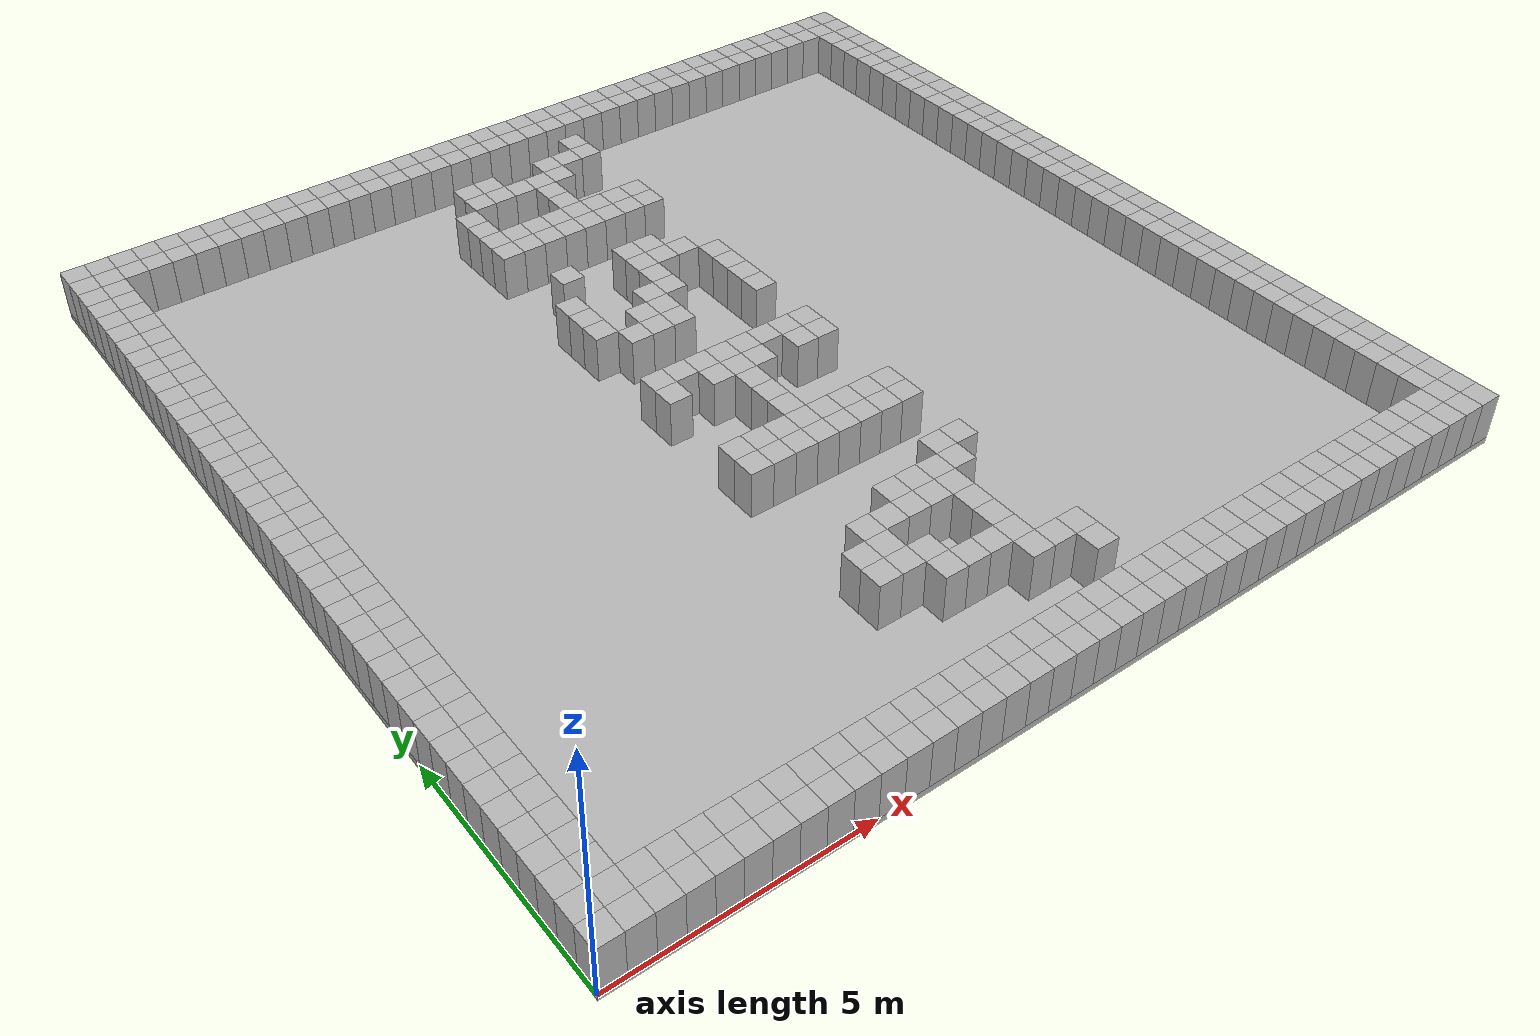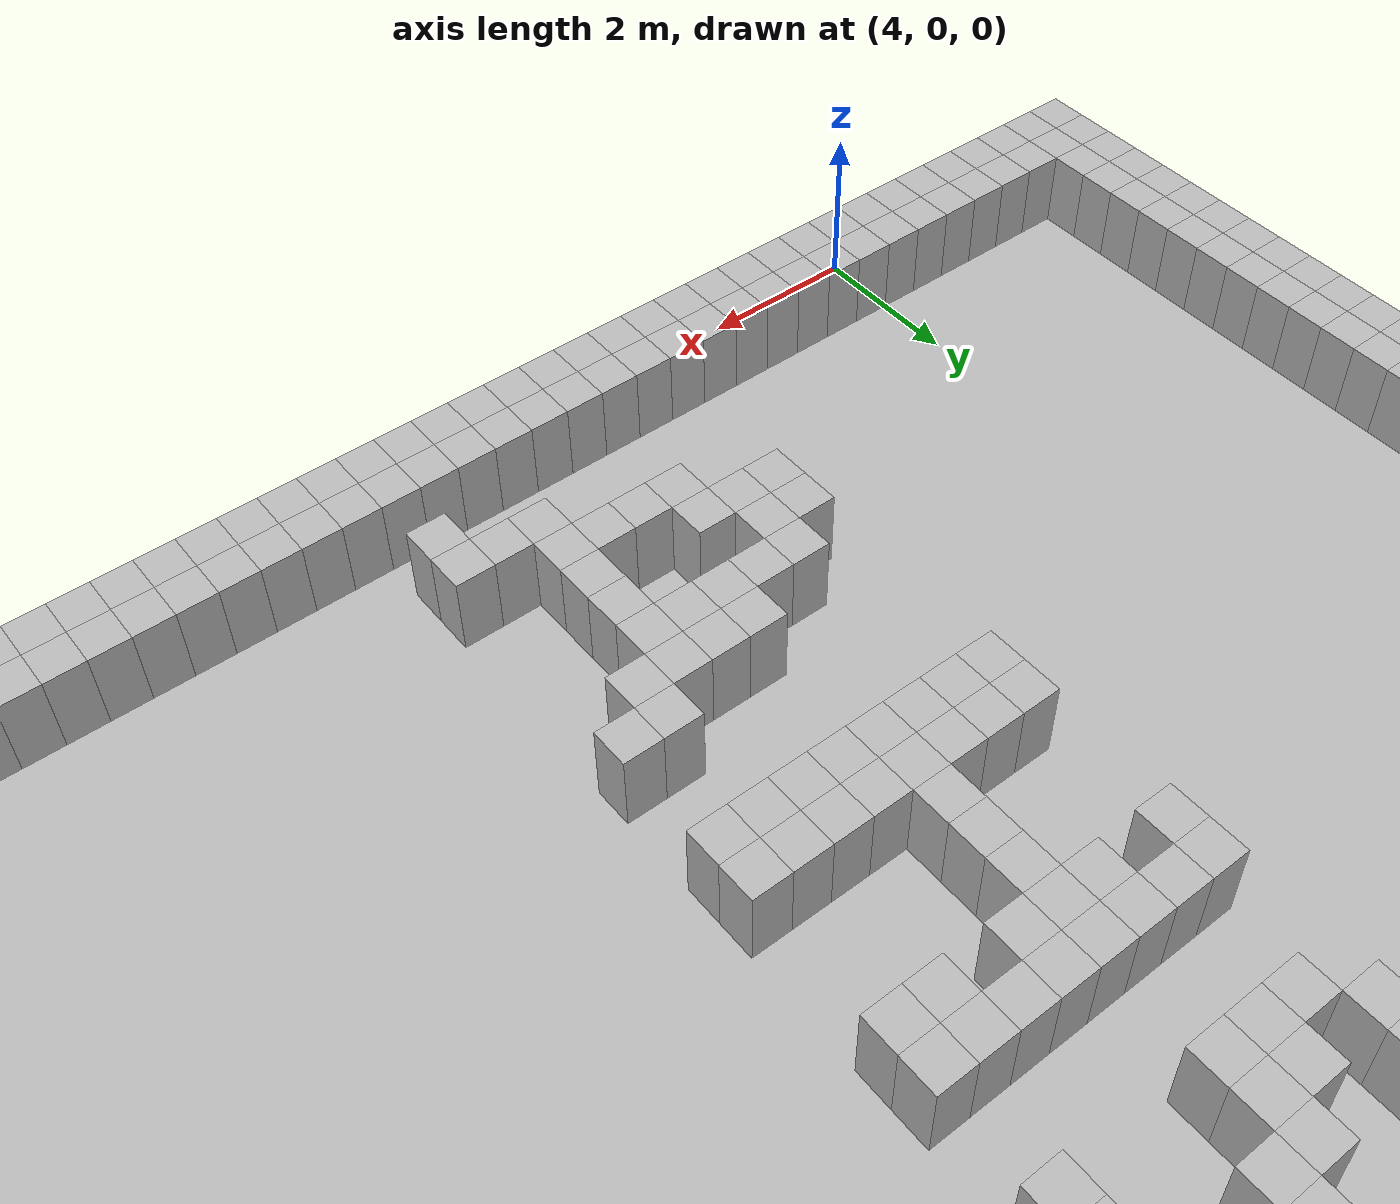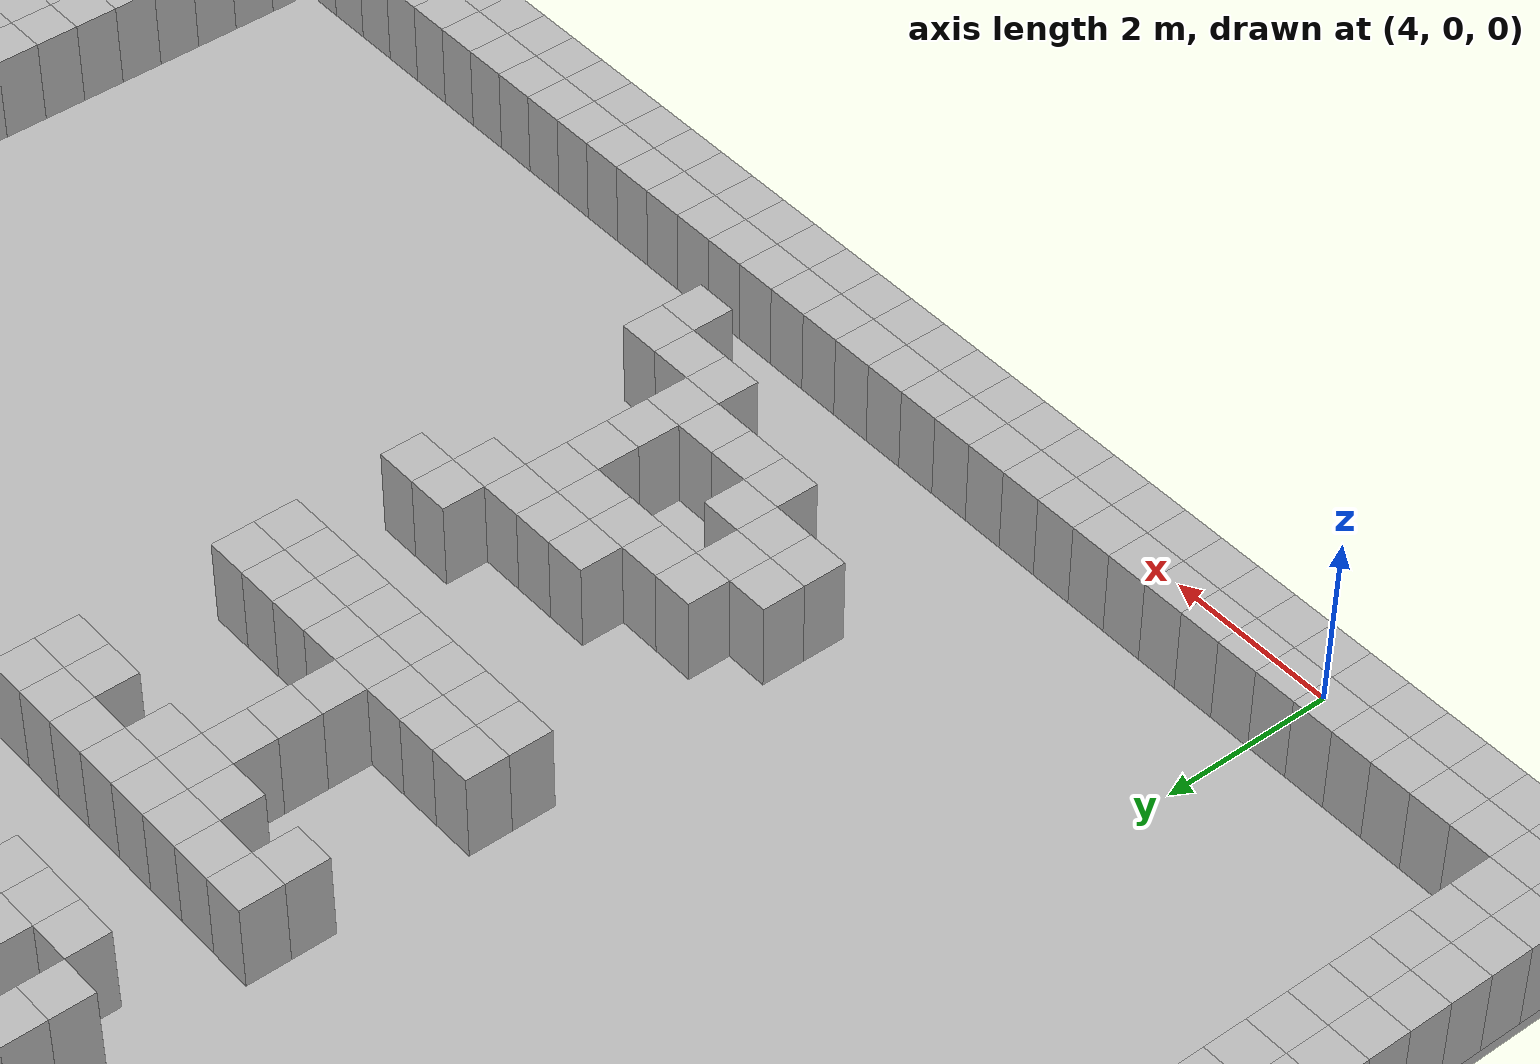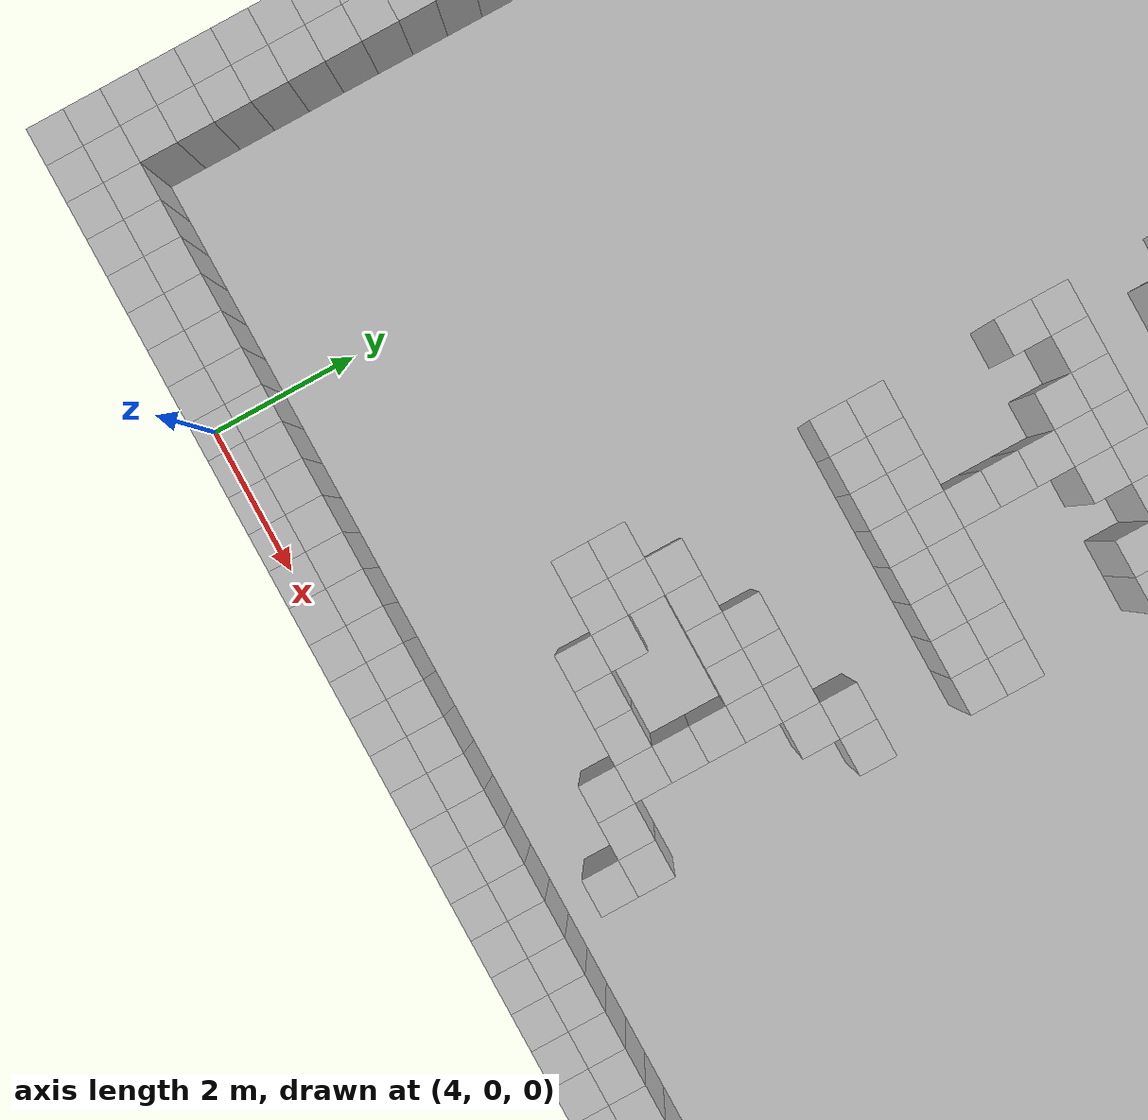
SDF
<sdf version="1.5">
  <model name="map">
    <static>1</static>
    <link name="map">
      <collision name="floor">
        <pose>10.0 10.0 -0.0625 0 0 0</pose>
        <geometry>
          <box>
            <size>20.0 20.0 0.125</size>
          </box>
        </geometry>
      </collision>
      <visual name="floor">
        <pose>10.0 10.0 -0.0625 0 0 0</pose>
        <geometry>
          <box>
            <size>20.0 20.0 0.125</size>
          </box>
        </geometry>
      </visual>
      <collision name="box_0_0">
        <pose>0.25 0.25 0.5 0 0 0</pose>
        <geometry>
          <box>
            <size>0.5 0.5 1.0</size>
          </box>
        </geometry>
      </collision>
      <visual name="box_0_0">
        <pose>0.25 0.25 0.5 0 0 0</pose>
        <geometry>
          <box>
            <size>0.5 0.5 1.0</size>
          </box>
        </geometry>
      </visual>
      <collision name="box_0_1">
        <pose>0.25 0.75 0.5 0 0 0</pose>
        <geometry>
          <box>
            <size>0.5 0.5 1.0</size>
          </box>
        </geometry>
      </collision>
      <visual name="box_0_1">
        <pose>0.25 0.75 0.5 0 0 0</pose>
        <geometry>
          <box>
            <size>0.5 0.5 1.0</size>
          </box>
        </geometry>
      </visual>
      <collision name="box_0_2">
        <pose>0.25 1.25 0.5 0 0 0</pose>
        <geometry>
          <box>
            <size>0.5 0.5 1.0</size>
          </box>
        </geometry>
      </collision>
      <visual name="box_0_2">
        <pose>0.25 1.25 0.5 0 0 0</pose>
        <geometry>
          <box>
            <size>0.5 0.5 1.0</size>
          </box>
        </geometry>
      </visual>
      <collision name="box_0_3">
        <pose>0.25 1.75 0.5 0 0 0</pose>
        <geometry>
          <box>
            <size>0.5 0.5 1.0</size>
          </box>
        </geometry>
      </collision>
      <visual name="box_0_3">
        <pose>0.25 1.75 0.5 0 0 0</pose>
        <geometry>
          <box>
            <size>0.5 0.5 1.0</size>
          </box>
        </geometry>
      </visual>
      <collision name="box_0_4">
        <pose>0.25 2.25 0.5 0 0 0</pose>
        <geometry>
          <box>
            <size>0.5 0.5 1.0</size>
          </box>
        </geometry>
      </collision>
      <visual name="box_0_4">
        <pose>0.25 2.25 0.5 0 0 0</pose>
        <geometry>
          <box>
            <size>0.5 0.5 1.0</size>
          </box>
        </geometry>
      </visual>
      <collision name="box_0_5">
        <pose>0.25 2.75 0.5 0 0 0</pose>
        <geometry>
          <box>
            <size>0.5 0.5 1.0</size>
          </box>
        </geometry>
      </collision>
      <visual name="box_0_5">
        <pose>0.25 2.75 0.5 0 0 0</pose>
        <geometry>
          <box>
            <size>0.5 0.5 1.0</size>
          </box>
        </geometry>
      </visual>
      <collision name="box_0_6">
        <pose>0.25 3.25 0.5 0 0 0</pose>
        <geometry>
          <box>
            <size>0.5 0.5 1.0</size>
          </box>
        </geometry>
      </collision>
      <visual name="box_0_6">
        <pose>0.25 3.25 0.5 0 0 0</pose>
        <geometry>
          <box>
            <size>0.5 0.5 1.0</size>
          </box>
        </geometry>
      </visual>
      <collision name="box_0_7">
        <pose>0.25 3.75 0.5 0 0 0</pose>
        <geometry>
          <box>
            <size>0.5 0.5 1.0</size>
          </box>
        </geometry>
      </collision>
      <visual name="box_0_7">
        <pose>0.25 3.75 0.5 0 0 0</pose>
        <geometry>
          <box>
            <size>0.5 0.5 1.0</size>
          </box>
        </geometry>
      </visual>
      <collision name="box_0_8">
        <pose>0.25 4.25 0.5 0 0 0</pose>
        <geometry>
          <box>
            <size>0.5 0.5 1.0</size>
          </box>
        </geometry>
      </collision>
      <visual name="box_0_8">
        <pose>0.25 4.25 0.5 0 0 0</pose>
        <geometry>
          <box>
            <size>0.5 0.5 1.0</size>
          </box>
        </geometry>
      </visual>
      <collision name="box_0_9">
        <pose>0.25 4.75 0.5 0 0 0</pose>
        <geometry>
          <box>
            <size>0.5 0.5 1.0</size>
          </box>
        </geometry>
      </collision>
      <visual name="box_0_9">
        <pose>0.25 4.75 0.5 0 0 0</pose>
        <geometry>
          <box>
            <size>0.5 0.5 1.0</size>
          </box>
        </geometry>
      </visual>
      <collision name="box_0_10">
        <pose>0.25 5.25 0.5 0 0 0</pose>
        <geometry>
          <box>
            <size>0.5 0.5 1.0</size>
          </box>
        </geometry>
      </collision>
      <visual name="box_0_10">
        <pose>0.25 5.25 0.5 0 0 0</pose>
        <geometry>
          <box>
            <size>0.5 0.5 1.0</size>
          </box>
        </geometry>
      </visual>
      <collision name="box_0_11">
        <pose>0.25 5.75 0.5 0 0 0</pose>
        <geometry>
          <box>
            <size>0.5 0.5 1.0</size>
          </box>
        </geometry>
      </collision>
      <visual name="box_0_11">
        <pose>0.25 5.75 0.5 0 0 0</pose>
        <geometry>
          <box>
            <size>0.5 0.5 1.0</size>
          </box>
        </geometry>
      </visual>
      <collision name="box_0_12">
        <pose>0.25 6.25 0.5 0 0 0</pose>
        <geometry>
          <box>
            <size>0.5 0.5 1.0</size>
          </box>
        </geometry>
      </collision>
      <visual name="box_0_12">
        <pose>0.25 6.25 0.5 0 0 0</pose>
        <geometry>
          <box>
            <size>0.5 0.5 1.0</size>
          </box>
        </geometry>
      </visual>
      <collision name="box_0_13">
        <pose>0.25 6.75 0.5 0 0 0</pose>
        <geometry>
          <box>
            <size>0.5 0.5 1.0</size>
          </box>
        </geometry>
      </collision>
      <visual name="box_0_13">
        <pose>0.25 6.75 0.5 0 0 0</pose>
        <geometry>
          <box>
            <size>0.5 0.5 1.0</size>
          </box>
        </geometry>
      </visual>
      <collision name="box_0_14">
        <pose>0.25 7.25 0.5 0 0 0</pose>
        <geometry>
          <box>
            <size>0.5 0.5 1.0</size>
          </box>
        </geometry>
      </collision>
      <visual name="box_0_14">
        <pose>0.25 7.25 0.5 0 0 0</pose>
        <geometry>
          <box>
            <size>0.5 0.5 1.0</size>
          </box>
        </geometry>
      </visual>
      <collision name="box_0_15">
        <pose>0.25 7.75 0.5 0 0 0</pose>
        <geometry>
          <box>
            <size>0.5 0.5 1.0</size>
          </box>
        </geometry>
      </collision>
      <visual name="box_0_15">
        <pose>0.25 7.75 0.5 0 0 0</pose>
        <geometry>
          <box>
            <size>0.5 0.5 1.0</size>
          </box>
        </geometry>
      </visual>
      <collision name="box_0_16">
        <pose>0.25 8.25 0.5 0 0 0</pose>
        <geometry>
          <box>
            <size>0.5 0.5 1.0</size>
          </box>
        </geometry>
      </collision>
      <visual name="box_0_16">
        <pose>0.25 8.25 0.5 0 0 0</pose>
        <geometry>
          <box>
            <size>0.5 0.5 1.0</size>
          </box>
        </geometry>
      </visual>
      <collision name="box_0_17">
        <pose>0.25 8.75 0.5 0 0 0</pose>
        <geometry>
          <box>
            <size>0.5 0.5 1.0</size>
          </box>
        </geometry>
      </collision>
      <visual name="box_0_17">
        <pose>0.25 8.75 0.5 0 0 0</pose>
        <geometry>
          <box>
            <size>0.5 0.5 1.0</size>
          </box>
        </geometry>
      </visual>
      <collision name="box_0_18">
        <pose>0.25 9.25 0.5 0 0 0</pose>
        <geometry>
          <box>
            <size>0.5 0.5 1.0</size>
          </box>
        </geometry>
      </collision>
      <visual name="box_0_18">
        <pose>0.25 9.25 0.5 0 0 0</pose>
        <geometry>
          <box>
            <size>0.5 0.5 1.0</size>
          </box>
        </geometry>
      </visual>
      <collision name="box_0_19">
        <pose>0.25 9.75 0.5 0 0 0</pose>
        <geometry>
          <box>
            <size>0.5 0.5 1.0</size>
          </box>
        </geometry>
      </collision>
      <visual name="box_0_19">
        <pose>0.25 9.75 0.5 0 0 0</pose>
        <geometry>
          <box>
            <size>0.5 0.5 1.0</size>
          </box>
        </geometry>
      </visual>
      <collision name="box_0_20">
        <pose>0.25 10.25 0.5 0 0 0</pose>
        <geometry>
          <box>
            <size>0.5 0.5 1.0</size>
          </box>
        </geometry>
      </collision>
      <visual name="box_0_20">
        <pose>0.25 10.25 0.5 0 0 0</pose>
        <geometry>
          <box>
            <size>0.5 0.5 1.0</size>
          </box>
        </geometry>
      </visual>
      <collision name="box_0_21">
        <pose>0.25 10.75 0.5 0 0 0</pose>
        <geometry>
          <box>
            <size>0.5 0.5 1.0</size>
          </box>
        </geometry>
      </collision>
      <visual name="box_0_21">
        <pose>0.25 10.75 0.5 0 0 0</pose>
        <geometry>
          <box>
            <size>0.5 0.5 1.0</size>
          </box>
        </geometry>
      </visual>
      <collision name="box_0_22">
        <pose>0.25 11.25 0.5 0 0 0</pose>
        <geometry>
          <box>
            <size>0.5 0.5 1.0</size>
          </box>
        </geometry>
      </collision>
      <visual name="box_0_22">
        <pose>0.25 11.25 0.5 0 0 0</pose>
        <geometry>
          <box>
            <size>0.5 0.5 1.0</size>
          </box>
        </geometry>
      </visual>
      <collision name="box_0_23">
        <pose>0.25 11.75 0.5 0 0 0</pose>
        <geometry>
          <box>
            <size>0.5 0.5 1.0</size>
          </box>
        </geometry>
      </collision>
      <visual name="box_0_23">
        <pose>0.25 11.75 0.5 0 0 0</pose>
        <geometry>
          <box>
            <size>0.5 0.5 1.0</size>
          </box>
        </geometry>
      </visual>
      <collision name="box_0_24">
        <pose>0.25 12.25 0.5 0 0 0</pose>
        <geometry>
          <box>
            <size>0.5 0.5 1.0</size>
          </box>
        </geometry>
      </collision>
      <visual name="box_0_24">
        <pose>0.25 12.25 0.5 0 0 0</pose>
        <geometry>
          <box>
            <size>0.5 0.5 1.0</size>
          </box>
        </geometry>
      </visual>
      <collision name="box_0_25">
        <pose>0.25 12.75 0.5 0 0 0</pose>
        <geometry>
          <box>
            <size>0.5 0.5 1.0</size>
          </box>
        </geometry>
      </collision>
      <visual name="box_0_25">
        <pose>0.25 12.75 0.5 0 0 0</pose>
        <geometry>
          <box>
            <size>0.5 0.5 1.0</size>
          </box>
        </geometry>
      </visual>
      <collision name="box_0_26">
        <pose>0.25 13.25 0.5 0 0 0</pose>
        <geometry>
          <box>
            <size>0.5 0.5 1.0</size>
          </box>
        </geometry>
      </collision>
      <visual name="box_0_26">
        <pose>0.25 13.25 0.5 0 0 0</pose>
        <geometry>
          <box>
            <size>0.5 0.5 1.0</size>
          </box>
        </geometry>
      </visual>
      <collision name="box_0_27">
        <pose>0.25 13.75 0.5 0 0 0</pose>
        <geometry>
          <box>
            <size>0.5 0.5 1.0</size>
          </box>
        </geometry>
      </collision>
      <visual name="box_0_27">
        <pose>0.25 13.75 0.5 0 0 0</pose>
        <geometry>
          <box>
            <size>0.5 0.5 1.0</size>
          </box>
        </geometry>
      </visual>
      <collision name="box_0_28">
        <pose>0.25 14.25 0.5 0 0 0</pose>
        <geometry>
          <box>
            <size>0.5 0.5 1.0</size>
          </box>
        </geometry>
      </collision>
      <visual name="box_0_28">
        <pose>0.25 14.25 0.5 0 0 0</pose>
        <geometry>
          <box>
            <size>0.5 0.5 1.0</size>
          </box>
        </geometry>
      </visual>
      <collision name="box_0_29">
        <pose>0.25 14.75 0.5 0 0 0</pose>
        <geometry>
          <box>
            <size>0.5 0.5 1.0</size>
          </box>
        </geometry>
      </collision>
      <visual name="box_0_29">
        <pose>0.25 14.75 0.5 0 0 0</pose>
        <geometry>
          <box>
            <size>0.5 0.5 1.0</size>
          </box>
        </geometry>
      </visual>
      <collision name="box_0_30">
        <pose>0.25 15.25 0.5 0 0 0</pose>
        <geometry>
          <box>
            <size>0.5 0.5 1.0</size>
          </box>
        </geometry>
      </collision>
      <visual name="box_0_30">
        <pose>0.25 15.25 0.5 0 0 0</pose>
        <geometry>
          <box>
            <size>0.5 0.5 1.0</size>
          </box>
        </geometry>
      </visual>
      <collision name="box_0_31">
        <pose>0.25 15.75 0.5 0 0 0</pose>
        <geometry>
          <box>
            <size>0.5 0.5 1.0</size>
          </box>
        </geometry>
      </collision>
      <visual name="box_0_31">
        <pose>0.25 15.75 0.5 0 0 0</pose>
        <geometry>
          <box>
            <size>0.5 0.5 1.0</size>
          </box>
        </geometry>
      </visual>
      <collision name="box_0_32">
        <pose>0.25 16.25 0.5 0 0 0</pose>
        <geometry>
          <box>
            <size>0.5 0.5 1.0</size>
          </box>
        </geometry>
      </collision>
      <visual name="box_0_32">
        <pose>0.25 16.25 0.5 0 0 0</pose>
        <geometry>
          <box>
            <size>0.5 0.5 1.0</size>
          </box>
        </geometry>
      </visual>
      <collision name="box_0_33">
        <pose>0.25 16.75 0.5 0 0 0</pose>
        <geometry>
          <box>
            <size>0.5 0.5 1.0</size>
          </box>
        </geometry>
      </collision>
      <visual name="box_0_33">
        <pose>0.25 16.75 0.5 0 0 0</pose>
        <geometry>
          <box>
            <size>0.5 0.5 1.0</size>
          </box>
        </geometry>
      </visual>
      <collision name="box_0_34">
        <pose>0.25 17.25 0.5 0 0 0</pose>
        <geometry>
          <box>
            <size>0.5 0.5 1.0</size>
          </box>
        </geometry>
      </collision>
      <visual name="box_0_34">
        <pose>0.25 17.25 0.5 0 0 0</pose>
        <geometry>
          <box>
            <size>0.5 0.5 1.0</size>
          </box>
        </geometry>
      </visual>
      <collision name="box_0_35">
        <pose>0.25 17.75 0.5 0 0 0</pose>
        <geometry>
          <box>
            <size>0.5 0.5 1.0</size>
          </box>
        </geometry>
      </collision>
      <visual name="box_0_35">
        <pose>0.25 17.75 0.5 0 0 0</pose>
        <geometry>
          <box>
            <size>0.5 0.5 1.0</size>
          </box>
        </geometry>
      </visual>
      <collision name="box_0_36">
        <pose>0.25 18.25 0.5 0 0 0</pose>
        <geometry>
          <box>
            <size>0.5 0.5 1.0</size>
          </box>
        </geometry>
      </collision>
      <visual name="box_0_36">
        <pose>0.25 18.25 0.5 0 0 0</pose>
        <geometry>
          <box>
            <size>0.5 0.5 1.0</size>
          </box>
        </geometry>
      </visual>
      <collision name="box_0_37">
        <pose>0.25 18.75 0.5 0 0 0</pose>
        <geometry>
          <box>
            <size>0.5 0.5 1.0</size>
          </box>
        </geometry>
      </collision>
      <visual name="box_0_37">
        <pose>0.25 18.75 0.5 0 0 0</pose>
        <geometry>
          <box>
            <size>0.5 0.5 1.0</size>
          </box>
        </geometry>
      </visual>
      <collision name="box_0_38">
        <pose>0.25 19.25 0.5 0 0 0</pose>
        <geometry>
          <box>
            <size>0.5 0.5 1.0</size>
          </box>
        </geometry>
      </collision>
      <visual name="box_0_38">
        <pose>0.25 19.25 0.5 0 0 0</pose>
        <geometry>
          <box>
            <size>0.5 0.5 1.0</size>
          </box>
        </geometry>
      </visual>
      <collision name="box_0_39">
        <pose>0.25 19.75 0.5 0 0 0</pose>
        <geometry>
          <box>
            <size>0.5 0.5 1.0</size>
          </box>
        </geometry>
      </collision>
      <visual name="box_0_39">
        <pose>0.25 19.75 0.5 0 0 0</pose>
        <geometry>
          <box>
            <size>0.5 0.5 1.0</size>
          </box>
        </geometry>
      </visual>
      <collision name="box_1_0">
        <pose>0.75 0.25 0.5 0 0 0</pose>
        <geometry>
          <box>
            <size>0.5 0.5 1.0</size>
          </box>
        </geometry>
      </collision>
      <visual name="box_1_0">
        <pose>0.75 0.25 0.5 0 0 0</pose>
        <geometry>
          <box>
            <size>0.5 0.5 1.0</size>
          </box>
        </geometry>
      </visual>
      <collision name="box_1_1">
        <pose>0.75 0.75 0.5 0 0 0</pose>
        <geometry>
          <box>
            <size>0.5 0.5 1.0</size>
          </box>
        </geometry>
      </collision>
      <visual name="box_1_1">
        <pose>0.75 0.75 0.5 0 0 0</pose>
        <geometry>
          <box>
            <size>0.5 0.5 1.0</size>
          </box>
        </geometry>
      </visual>
      <collision name="box_1_2">
        <pose>0.75 1.25 0.5 0 0 0</pose>
        <geometry>
          <box>
            <size>0.5 0.5 1.0</size>
          </box>
        </geometry>
      </collision>
      <visual name="box_1_2">
        <pose>0.75 1.25 0.5 0 0 0</pose>
        <geometry>
          <box>
            <size>0.5 0.5 1.0</size>
          </box>
        </geometry>
      </visual>
      <collision name="box_1_3">
        <pose>0.75 1.75 0.5 0 0 0</pose>
        <geometry>
          <box>
            <size>0.5 0.5 1.0</size>
          </box>
        </geometry>
      </collision>
      <visual name="box_1_3">
        <pose>0.75 1.75 0.5 0 0 0</pose>
        <geometry>
          <box>
            <size>0.5 0.5 1.0</size>
          </box>
        </geometry>
      </visual>
      <collision name="box_1_4">
        <pose>0.75 2.25 0.5 0 0 0</pose>
        <geometry>
          <box>
            <size>0.5 0.5 1.0</size>
          </box>
        </geometry>
      </collision>
      <visual name="box_1_4">
        <pose>0.75 2.25 0.5 0 0 0</pose>
        <geometry>
          <box>
            <size>0.5 0.5 1.0</size>
          </box>
        </geometry>
      </visual>
      <collision name="box_1_5">
        <pose>0.75 2.75 0.5 0 0 0</pose>
        <geometry>
          <box>
            <size>0.5 0.5 1.0</size>
          </box>
        </geometry>
      </collision>
      <visual name="box_1_5">
        <pose>0.75 2.75 0.5 0 0 0</pose>
        <geometry>
          <box>
            <size>0.5 0.5 1.0</size>
          </box>
        </geometry>
      </visual>
      <collision name="box_1_6">
        <pose>0.75 3.25 0.5 0 0 0</pose>
        <geometry>
          <box>
            <size>0.5 0.5 1.0</size>
          </box>
        </geometry>
      </collision>
      <visual name="box_1_6">
        <pose>0.75 3.25 0.5 0 0 0</pose>
        <geometry>
          <box>
            <size>0.5 0.5 1.0</size>
          </box>
        </geometry>
      </visual>
      <collision name="box_1_7">
        <pose>0.75 3.75 0.5 0 0 0</pose>
        <geometry>
          <box>
            <size>0.5 0.5 1.0</size>
          </box>
        </geometry>
      </collision>
      <visual name="box_1_7">
        <pose>0.75 3.75 0.5 0 0 0</pose>
        <geometry>
          <box>
            <size>0.5 0.5 1.0</size>
          </box>
        </geometry>
      </visual>
      <collision name="box_1_8">
        <pose>0.75 4.25 0.5 0 0 0</pose>
        <geometry>
          <box>
            <size>0.5 0.5 1.0</size>
          </box>
        </geometry>
      </collision>
      <visual name="box_1_8">
        <pose>0.75 4.25 0.5 0 0 0</pose>
        <geometry>
          <box>
            <size>0.5 0.5 1.0</size>
          </box>
        </geometry>
      </visual>
      <collision name="box_1_9">
        <pose>0.75 4.75 0.5 0 0 0</pose>
        <geometry>
          <box>
            <size>0.5 0.5 1.0</size>
          </box>
        </geometry>
      </collision>
      <visual name="box_1_9">
        <pose>0.75 4.75 0.5 0 0 0</pose>
        <geometry>
          <box>
            <size>0.5 0.5 1.0</size>
          </box>
        </geometry>
      </visual>
      <collision name="box_1_10">
        <pose>0.75 5.25 0.5 0 0 0</pose>
        <geometry>
          <box>
            <size>0.5 0.5 1.0</size>
          </box>
        </geometry>
      </collision>
      <visual name="box_1_10">
        <pose>0.75 5.25 0.5 0 0 0</pose>
        <geometry>
          <box>
            <size>0.5 0.5 1.0</size>
          </box>
        </geometry>
      </visual>
      <collision name="box_1_11">
        <pose>0.75 5.75 0.5 0 0 0</pose>
        <geometry>
          <box>
            <size>0.5 0.5 1.0</size>
          </box>
        </geometry>
      </collision>
      <visual name="box_1_11">
        <pose>0.75 5.75 0.5 0 0 0</pose>
        <geometry>
          <box>
            <size>0.5 0.5 1.0</size>
          </box>
        </geometry>
      </visual>
      <collision name="box_1_12">
        <pose>0.75 6.25 0.5 0 0 0</pose>
        <geometry>
          <box>
            <size>0.5 0.5 1.0</size>
          </box>
        </geometry>
      </collision>
      <visual name="box_1_12">
        <pose>0.75 6.25 0.5 0 0 0</pose>
        <geometry>
          <box>
            <size>0.5 0.5 1.0</size>
          </box>
        </geometry>
      </visual>
      <collision name="box_1_13">
        <pose>0.75 6.75 0.5 0 0 0</pose>
        <geometry>
          <box>
            <size>0.5 0.5 1.0</size>
          </box>
        </geometry>
      </collision>
      <visual name="box_1_13">
        <pose>0.75 6.75 0.5 0 0 0</pose>
        <geometry>
          <box>
            <size>0.5 0.5 1.0</size>
          </box>
        </geometry>
      </visual>
      <collision name="box_1_14">
        <pose>0.75 7.25 0.5 0 0 0</pose>
        <geometry>
          <box>
            <size>0.5 0.5 1.0</size>
          </box>
        </geometry>
      </collision>
      <visual name="box_1_14">
        <pose>0.75 7.25 0.5 0 0 0</pose>
        <geometry>
          <box>
            <size>0.5 0.5 1.0</size>
          </box>
        </geometry>
      </visual>
      <collision name="box_1_15">
        <pose>0.75 7.75 0.5 0 0 0</pose>
        <geometry>
          <box>
            <size>0.5 0.5 1.0</size>
          </box>
        </geometry>
      </collision>
      <visual name="box_1_15">
        <pose>0.75 7.75 0.5 0 0 0</pose>
        <geometry>
          <box>
            <size>0.5 0.5 1.0</size>
          </box>
        </geometry>
      </visual>
      <collision name="box_1_16">
        <pose>0.75 8.25 0.5 0 0 0</pose>
        <geometry>
          <box>
            <size>0.5 0.5 1.0</size>
          </box>
        </geometry>
      </collision>
      <visual name="box_1_16">
        <pose>0.75 8.25 0.5 0 0 0</pose>
        <geometry>
          <box>
            <size>0.5 0.5 1.0</size>
          </box>
        </geometry>
      </visual>
      <collision name="box_1_17">
        <pose>0.75 8.75 0.5 0 0 0</pose>
        <geometry>
          <box>
            <size>0.5 0.5 1.0</size>
          </box>
        </geometry>
      </collision>
      <visual name="box_1_17">
        <pose>0.75 8.75 0.5 0 0 0</pose>
        <geometry>
          <box>
            <size>0.5 0.5 1.0</size>
          </box>
        </geometry>
      </visual>
      <collision name="box_1_18">
        <pose>0.75 9.25 0.5 0 0 0</pose>
        <geometry>
          <box>
            <size>0.5 0.5 1.0</size>
          </box>
        </geometry>
      </collision>
      <visual name="box_1_18">
        <pose>0.75 9.25 0.5 0 0 0</pose>
        <geometry>
          <box>
            <size>0.5 0.5 1.0</size>
          </box>
        </geometry>
      </visual>
      <collision name="box_1_19">
        <pose>0.75 9.75 0.5 0 0 0</pose>
        <geometry>
          <box>
            <size>0.5 0.5 1.0</size>
          </box>
        </geometry>
      </collision>
      <visual name="box_1_19">
        <pose>0.75 9.75 0.5 0 0 0</pose>
        <geometry>
          <box>
            <size>0.5 0.5 1.0</size>
          </box>
        </geometry>
      </visual>
      <collision name="box_1_20">
        <pose>0.75 10.25 0.5 0 0 0</pose>
        <geometry>
          <box>
            <size>0.5 0.5 1.0</size>
          </box>
        </geometry>
      </collision>
      <visual name="box_1_20">
        <pose>0.75 10.25 0.5 0 0 0</pose>
        <geometry>
          <box>
            <size>0.5 0.5 1.0</size>
          </box>
        </geometry>
      </visual>
      <collision name="box_1_21">
        <pose>0.75 10.75 0.5 0 0 0</pose>
        <geometry>
          <box>
            <size>0.5 0.5 1.0</size>
          </box>
        </geometry>
      </collision>
      <visual name="box_1_21">
        <pose>0.75 10.75 0.5 0 0 0</pose>
        <geometry>
          <box>
            <size>0.5 0.5 1.0</size>
          </box>
        </geometry>
      </visual>
      <collision name="box_1_22">
        <pose>0.75 11.25 0.5 0 0 0</pose>
        <geometry>
          <box>
            <size>0.5 0.5 1.0</size>
          </box>
        </geometry>
      </collision>
      <visual name="box_1_22">
        <pose>0.75 11.25 0.5 0 0 0</pose>
        <geometry>
          <box>
            <size>0.5 0.5 1.0</size>
          </box>
        </geometry>
      </visual>
      <collision name="box_1_23">
        <pose>0.75 11.75 0.5 0 0 0</pose>
        <geometry>
          <box>
            <size>0.5 0.5 1.0</size>
          </box>
        </geometry>
      </collision>
      <visual name="box_1_23">
        <pose>0.75 11.75 0.5 0 0 0</pose>
        <geometry>
          <box>
            <size>0.5 0.5 1.0</size>
          </box>
        </geometry>
      </visual>
      <collision name="box_1_24">
        <pose>0.75 12.25 0.5 0 0 0</pose>
        <geometry>
          <box>
            <size>0.5 0.5 1.0</size>
          </box>
        </geometry>
      </collision>
      <visual name="box_1_24">
        <pose>0.75 12.25 0.5 0 0 0</pose>
        <geometry>
          <box>
            <size>0.5 0.5 1.0</size>
          </box>
        </geometry>
      </visual>
      <collision name="box_1_25">
        <pose>0.75 12.75 0.5 0 0 0</pose>
        <geometry>
          <box>
            <size>0.5 0.5 1.0</size>
          </box>
        </geometry>
      </collision>
      <visual name="box_1_25">
        <pose>0.75 12.75 0.5 0 0 0</pose>
        <geometry>
          <box>
            <size>0.5 0.5 1.0</size>
          </box>
        </geometry>
      </visual>
      <collision name="box_1_26">
        <pose>0.75 13.25 0.5 0 0 0</pose>
        <geometry>
          <box>
            <size>0.5 0.5 1.0</size>
          </box>
        </geometry>
      </collision>
      <visual name="box_1_26">
        <pose>0.75 13.25 0.5 0 0 0</pose>
        <geometry>
          <box>
            <size>0.5 0.5 1.0</size>
          </box>
        </geometry>
      </visual>
      <collision name="box_1_27">
        <pose>0.75 13.75 0.5 0 0 0</pose>
        <geometry>
          <box>
            <size>0.5 0.5 1.0</size>
          </box>
        </geometry>
      </collision>
      <visual name="box_1_27">
        <pose>0.75 13.75 0.5 0 0 0</pose>
        <geometry>
          <box>
            <size>0.5 0.5 1.0</size>
          </box>
        </geometry>
      </visual>
      <collision name="box_1_28">
        <pose>0.75 14.25 0.5 0 0 0</pose>
        <geometry>
          <box>
            <size>0.5 0.5 1.0</size>
          </box>
        </geometry>
      </collision>
      <visual name="box_1_28">
        <pose>0.75 14.25 0.5 0 0 0</pose>
        <geometry>
          <box>
            <size>0.5 0.5 1.0</size>
          </box>
        </geometry>
      </visual>
      <collision name="box_1_29">
        <pose>0.75 14.75 0.5 0 0 0</pose>
        <geometry>
          <box>
            <size>0.5 0.5 1.0</size>
          </box>
        </geometry>
      </collision>
      <visual name="box_1_29">
        <pose>0.75 14.75 0.5 0 0 0</pose>
        <geometry>
          <box>
            <size>0.5 0.5 1.0</size>
          </box>
        </geometry>
      </visual>
      <collision name="box_1_30">
        <pose>0.75 15.25 0.5 0 0 0</pose>
        <geometry>
          <box>
            <size>0.5 0.5 1.0</size>
          </box>
        </geometry>
      </collision>
      <visual name="box_1_30">
        <pose>0.75 15.25 0.5 0 0 0</pose>
        <geometry>
          <box>
            <size>0.5 0.5 1.0</size>
          </box>
        </geometry>
      </visual>
      <collision name="box_1_31">
        <pose>0.75 15.75 0.5 0 0 0</pose>
        <geometry>
          <box>
            <size>0.5 0.5 1.0</size>
          </box>
        </geometry>
      </collision>
      <visual name="box_1_31">
        <pose>0.75 15.75 0.5 0 0 0</pose>
        <geometry>
          <box>
            <size>0.5 0.5 1.0</size>
          </box>
        </geometry>
      </visual>
      <collision name="box_1_32">
        <pose>0.75 16.25 0.5 0 0 0</pose>
        <geometry>
          <box>
            <size>0.5 0.5 1.0</size>
          </box>
        </geometry>
      </collision>
      <visual name="box_1_32">
        <pose>0.75 16.25 0.5 0 0 0</pose>
        <geometry>
          <box>
            <size>0.5 0.5 1.0</size>
          </box>
        </geometry>
      </visual>
      <collision name="box_1_33">
        <pose>0.75 16.75 0.5 0 0 0</pose>
        <geometry>
          <box>
            <size>0.5 0.5 1.0</size>
          </box>
        </geometry>
      </collision>
      <visual name="box_1_33">
        <pose>0.75 16.75 0.5 0 0 0</pose>
        <geometry>
          <box>
            <size>0.5 0.5 1.0</size>
          </box>
        </geometry>
      </visual>
      <collision name="box_1_34">
        <pose>0.75 17.25 0.5 0 0 0</pose>
        <geometry>
          <box>
            <size>0.5 0.5 1.0</size>
          </box>
        </geometry>
      </collision>
      <visual name="box_1_34">
        <pose>0.75 17.25 0.5 0 0 0</pose>
        <geometry>
          <box>
            <size>0.5 0.5 1.0</size>
          </box>
        </geometry>
      </visual>
      <collision name="box_1_35">
        <pose>0.75 17.75 0.5 0 0 0</pose>
        <geometry>
          <box>
            <size>0.5 0.5 1.0</size>
          </box>
        </geometry>
      </collision>
      <visual name="box_1_35">
        <pose>0.75 17.75 0.5 0 0 0</pose>
        <geometry>
          <box>
            <size>0.5 0.5 1.0</size>
          </box>
        </geometry>
      </visual>
      <collision name="box_1_36">
        <pose>0.75 18.25 0.5 0 0 0</pose>
        <geometry>
          <box>
            <size>0.5 0.5 1.0</size>
          </box>
        </geometry>
      </collision>
      <visual name="box_1_36">
        <pose>0.75 18.25 0.5 0 0 0</pose>
        <geometry>
          <box>
            <size>0.5 0.5 1.0</size>
          </box>
        </geometry>
      </visual>
      <collision name="box_1_37">
        <pose>0.75 18.75 0.5 0 0 0</pose>
        <geometry>
          <box>
            <size>0.5 0.5 1.0</size>
          </box>
        </geometry>
      </collision>
      <visual name="box_1_37">
        <pose>0.75 18.75 0.5 0 0 0</pose>
        <geometry>
          <box>
            <size>0.5 0.5 1.0</size>
          </box>
        </geometry>
      </visual>
      <collision name="box_1_38">
        <pose>0.75 19.25 0.5 0 0 0</pose>
        <geometry>
          <box>
            <size>0.5 0.5 1.0</size>
          </box>
        </geometry>
      </collision>
      <visual name="box_1_38">
        <pose>0.75 19.25 0.5 0 0 0</pose>
        <geometry>
          <box>
            <size>0.5 0.5 1.0</size>
          </box>
        </geometry>
      </visual>
      <collision name="box_1_39">
        <pose>0.75 19.75 0.5 0 0 0</pose>
        <geometry>
          <box>
            <size>0.5 0.5 1.0</size>
          </box>
        </geometry>
      </collision>
      <visual name="box_1_39">
        <pose>0.75 19.75 0.5 0 0 0</pose>
        <geometry>
          <box>
            <size>0.5 0.5 1.0</size>
          </box>
        </geometry>
      </visual>
      <collision name="box_2_0">
        <pose>1.25 0.25 0.5 0 0 0</pose>
        <geometry>
          <box>
            <size>0.5 0.5 1.0</size>
          </box>
        </geometry>
      </collision>
      <visual name="box_2_0">
        <pose>1.25 0.25 0.5 0 0 0</pose>
        <geometry>
          <box>
            <size>0.5 0.5 1.0</size>
          </box>
        </geometry>
      </visual>
      <collision name="box_2_1">
        <pose>1.25 0.75 0.5 0 0 0</pose>
        <geometry>
          <box>
            <size>0.5 0.5 1.0</size>
          </box>
        </geometry>
      </collision>
      <visual name="box_2_1">
        <pose>1.25 0.75 0.5 0 0 0</pose>
        <geometry>
          <box>
            <size>0.5 0.5 1.0</size>
          </box>
        </geometry>
      </visual>
      <collision name="box_2_38">
        <pose>1.25 19.25 0.5 0 0 0</pose>
        <geometry>
          <box>
            <size>0.5 0.5 1.0</size>
          </box>
        </geometry>
      </collision>
      <visual name="box_2_38">
        <pose>1.25 19.25 0.5 0 0 0</pose>
        <geometry>
          <box>
            <size>0.5 0.5 1.0</size>
          </box>
        </geometry>
      </visual>
      <collision name="box_2_39">
        <pose>1.25 19.75 0.5 0 0 0</pose>
        <geometry>
          <box>
            <size>0.5 0.5 1.0</size>
          </box>
        </geometry>
      </collision>
      <visual name="box_2_39">
        <pose>1.25 19.75 0.5 0 0 0</pose>
        <geometry>
          <box>
            <size>0.5 0.5 1.0</size>
          </box>
        </geometry>
      </visual>
      <collision name="box_3_0">
        <pose>1.75 0.25 0.5 0 0 0</pose>
        <geometry>
          <box>
            <size>0.5 0.5 1.0</size>
          </box>
        </geometry>
      </collision>
      <visual name="box_3_0">
        <pose>1.75 0.25 0.5 0 0 0</pose>
        <geometry>
          <box>
            <size>0.5 0.5 1.0</size>
          </box>
        </geometry>
      </visual>
      <collision name="box_3_1">
        <pose>1.75 0.75 0.5 0 0 0</pose>
        <geometry>
          <box>
            <size>0.5 0.5 1.0</size>
          </box>
        </geometry>
      </collision>
      <visual name="box_3_1">
        <pose>1.75 0.75 0.5 0 0 0</pose>
        <geometry>
          <box>
            <size>0.5 0.5 1.0</size>
          </box>
        </geometry>
      </visual>
      <collision name="box_3_38">
        <pose>1.75 19.25 0.5 0 0 0</pose>
        <geometry>
          <box>
            <size>0.5 0.5 1.0</size>
          </box>
        </geometry>
      </collision>
      <visual name="box_3_38">
        <pose>1.75 19.25 0.5 0 0 0</pose>
        <geometry>
          <box>
            <size>0.5 0.5 1.0</size>
          </box>
        </geometry>
      </visual>
      <collision name="box_3_39">
        <pose>1.75 19.75 0.5 0 0 0</pose>
        <geometry>
          <box>
            <size>0.5 0.5 1.0</size>
          </box>
        </geometry>
      </collision>
      <visual name="box_3_39">
        <pose>1.75 19.75 0.5 0 0 0</pose>
        <geometry>
          <box>
            <size>0.5 0.5 1.0</size>
          </box>
        </geometry>
      </visual>
      <collision name="box_4_0">
        <pose>2.25 0.25 0.5 0 0 0</pose>
        <geometry>
          <box>
            <size>0.5 0.5 1.0</size>
          </box>
        </geometry>
      </collision>
      <visual name="box_4_0">
        <pose>2.25 0.25 0.5 0 0 0</pose>
        <geometry>
          <box>
            <size>0.5 0.5 1.0</size>
          </box>
        </geometry>
      </visual>
      <collision name="box_4_1">
        <pose>2.25 0.75 0.5 0 0 0</pose>
        <geometry>
          <box>
            <size>0.5 0.5 1.0</size>
          </box>
        </geometry>
      </collision>
      <visual name="box_4_1">
        <pose>2.25 0.75 0.5 0 0 0</pose>
        <geometry>
          <box>
            <size>0.5 0.5 1.0</size>
          </box>
        </geometry>
      </visual>
      <collision name="box_4_38">
        <pose>2.25 19.25 0.5 0 0 0</pose>
        <geometry>
          <box>
            <size>0.5 0.5 1.0</size>
          </box>
        </geometry>
      </collision>
      <visual name="box_4_38">
        <pose>2.25 19.25 0.5 0 0 0</pose>
        <geometry>
          <box>
            <size>0.5 0.5 1.0</size>
          </box>
        </geometry>
      </visual>
      <collision name="box_4_39">
        <pose>2.25 19.75 0.5 0 0 0</pose>
        <geometry>
          <box>
            <size>0.5 0.5 1.0</size>
          </box>
        </geometry>
      </collision>
      <visual name="box_4_39">
        <pose>2.25 19.75 0.5 0 0 0</pose>
        <geometry>
          <box>
            <size>0.5 0.5 1.0</size>
          </box>
        </geometry>
      </visual>
      <collision name="box_5_0">
        <pose>2.75 0.25 0.5 0 0 0</pose>
        <geometry>
          <box>
            <size>0.5 0.5 1.0</size>
          </box>
        </geometry>
      </collision>
      <visual name="box_5_0">
        <pose>2.75 0.25 0.5 0 0 0</pose>
        <geometry>
          <box>
            <size>0.5 0.5 1.0</size>
          </box>
        </geometry>
      </visual>
      <collision name="box_5_1">
        <pose>2.75 0.75 0.5 0 0 0</pose>
        <geometry>
          <box>
            <size>0.5 0.5 1.0</size>
          </box>
        </geometry>
      </collision>
      <visual name="box_5_1">
        <pose>2.75 0.75 0.5 0 0 0</pose>
        <geometry>
          <box>
            <size>0.5 0.5 1.0</size>
          </box>
        </geometry>
      </visual>
      <collision name="box_5_38">
        <pose>2.75 19.25 0.5 0 0 0</pose>
        <geometry>
          <box>
            <size>0.5 0.5 1.0</size>
          </box>
        </geometry>
      </collision>
      <visual name="box_5_38">
        <pose>2.75 19.25 0.5 0 0 0</pose>
        <geometry>
          <box>
            <size>0.5 0.5 1.0</size>
          </box>
        </geometry>
      </visual>
      <collision name="box_5_39">
        <pose>2.75 19.75 0.5 0 0 0</pose>
        <geometry>
          <box>
            <size>0.5 0.5 1.0</size>
          </box>
        </geometry>
      </collision>
      <visual name="box_5_39">
        <pose>2.75 19.75 0.5 0 0 0</pose>
        <geometry>
          <box>
            <size>0.5 0.5 1.0</size>
          </box>
        </geometry>
      </visual>
      <collision name="box_6_0">
        <pose>3.25 0.25 0.5 0 0 0</pose>
        <geometry>
          <box>
            <size>0.5 0.5 1.0</size>
          </box>
        </geometry>
      </collision>
      <visual name="box_6_0">
        <pose>3.25 0.25 0.5 0 0 0</pose>
        <geometry>
          <box>
            <size>0.5 0.5 1.0</size>
          </box>
        </geometry>
      </visual>
      <collision name="box_6_1">
        <pose>3.25 0.75 0.5 0 0 0</pose>
        <geometry>
          <box>
            <size>0.5 0.5 1.0</size>
          </box>
        </geometry>
      </collision>
      <visual name="box_6_1">
        <pose>3.25 0.75 0.5 0 0 0</pose>
        <geometry>
          <box>
            <size>0.5 0.5 1.0</size>
          </box>
        </geometry>
      </visual>
      <collision name="box_6_38">
        <pose>3.25 19.25 0.5 0 0 0</pose>
        <geometry>
          <box>
            <size>0.5 0.5 1.0</size>
          </box>
        </geometry>
      </collision>
      <visual name="box_6_38">
        <pose>3.25 19.25 0.5 0 0 0</pose>
        <geometry>
          <box>
            <size>0.5 0.5 1.0</size>
          </box>
        </geometry>
      </visual>
      <collision name="box_6_39">
        <pose>3.25 19.75 0.5 0 0 0</pose>
        <geometry>
          <box>
            <size>0.5 0.5 1.0</size>
          </box>
        </geometry>
      </collision>
      <visual name="box_6_39">
        <pose>3.25 19.75 0.5 0 0 0</pose>
        <geometry>
          <box>
            <size>0.5 0.5 1.0</size>
          </box>
        </geometry>
      </visual>
      <collision name="box_7_0">
        <pose>3.75 0.25 0.5 0 0 0</pose>
        <geometry>
          <box>
            <size>0.5 0.5 1.0</size>
          </box>
        </geometry>
      </collision>
      <visual name="box_7_0">
        <pose>3.75 0.25 0.5 0 0 0</pose>
        <geometry>
          <box>
            <size>0.5 0.5 1.0</size>
          </box>
        </geometry>
      </visual>
      <collision name="box_7_1">
        <pose>3.75 0.75 0.5 0 0 0</pose>
        <geometry>
          <box>
            <size>0.5 0.5 1.0</size>
          </box>
        </geometry>
      </collision>
      <visual name="box_7_1">
        <pose>3.75 0.75 0.5 0 0 0</pose>
        <geometry>
          <box>
            <size>0.5 0.5 1.0</size>
          </box>
        </geometry>
      </visual>
      <collision name="box_7_38">
        <pose>3.75 19.25 0.5 0 0 0</pose>
        <geometry>
          <box>
            <size>0.5 0.5 1.0</size>
          </box>
        </geometry>
      </collision>
      <visual name="box_7_38">
        <pose>3.75 19.25 0.5 0 0 0</pose>
        <geometry>
          <box>
            <size>0.5 0.5 1.0</size>
          </box>
        </geometry>
      </visual>
      <collision name="box_7_39">
        <pose>3.75 19.75 0.5 0 0 0</pose>
        <geometry>
          <box>
            <size>0.5 0.5 1.0</size>
          </box>
        </geometry>
      </collision>
      <visual name="box_7_39">
        <pose>3.75 19.75 0.5 0 0 0</pose>
        <geometry>
          <box>
            <size>0.5 0.5 1.0</size>
          </box>
        </geometry>
      </visual>
      <collision name="box_8_0">
        <pose>4.25 0.25 0.5 0 0 0</pose>
        <geometry>
          <box>
            <size>0.5 0.5 1.0</size>
          </box>
        </geometry>
      </collision>
      <visual name="box_8_0">
        <pose>4.25 0.25 0.5 0 0 0</pose>
        <geometry>
          <box>
            <size>0.5 0.5 1.0</size>
          </box>
        </geometry>
      </visual>
      <collision name="box_8_1">
        <pose>4.25 0.75 0.5 0 0 0</pose>
        <geometry>
          <box>
            <size>0.5 0.5 1.0</size>
          </box>
        </geometry>
      </collision>
      <visual name="box_8_1">
        <pose>4.25 0.75 0.5 0 0 0</pose>
        <geometry>
          <box>
            <size>0.5 0.5 1.0</size>
          </box>
        </geometry>
      </visual>
      <collision name="box_8_38">
        <pose>4.25 19.25 0.5 0 0 0</pose>
        <geometry>
          <box>
            <size>0.5 0.5 1.0</size>
          </box>
        </geometry>
      </collision>
      <visual name="box_8_38">
        <pose>4.25 19.25 0.5 0 0 0</pose>
        <geometry>
          <box>
            <size>0.5 0.5 1.0</size>
          </box>
        </geometry>
      </visual>
      <collision name="box_8_39">
        <pose>4.25 19.75 0.5 0 0 0</pose>
        <geometry>
          <box>
            <size>0.5 0.5 1.0</size>
          </box>
        </geometry>
      </collision>
      <visual name="box_8_39">
        <pose>4.25 19.75 0.5 0 0 0</pose>
        <geometry>
          <box>
            <size>0.5 0.5 1.0</size>
          </box>
        </geometry>
      </visual>
      <collision name="box_9_0">
        <pose>4.75 0.25 0.5 0 0 0</pose>
        <geometry>
          <box>
            <size>0.5 0.5 1.0</size>
          </box>
        </geometry>
      </collision>
      <visual name="box_9_0">
        <pose>4.75 0.25 0.5 0 0 0</pose>
        <geometry>
          <box>
            <size>0.5 0.5 1.0</size>
          </box>
        </geometry>
      </visual>
      <collision name="box_9_1">
        <pose>4.75 0.75 0.5 0 0 0</pose>
        <geometry>
          <box>
            <size>0.5 0.5 1.0</size>
          </box>
        </geometry>
      </collision>
      <visual name="box_9_1">
        <pose>4.75 0.75 0.5 0 0 0</pose>
        <geometry>
          <box>
            <size>0.5 0.5 1.0</size>
          </box>
        </geometry>
      </visual>
      <collision name="box_9_38">
        <pose>4.75 19.25 0.5 0 0 0</pose>
        <geometry>
          <box>
            <size>0.5 0.5 1.0</size>
          </box>
        </geometry>
      </collision>
      <visual name="box_9_38">
        <pose>4.75 19.25 0.5 0 0 0</pose>
        <geometry>
          <box>
            <size>0.5 0.5 1.0</size>
          </box>
        </geometry>
      </visual>
      <collision name="box_9_39">
        <pose>4.75 19.75 0.5 0 0 0</pose>
        <geometry>
          <box>
            <size>0.5 0.5 1.0</size>
          </box>
        </geometry>
      </collision>
      <visual name="box_9_39">
        <pose>4.75 19.75 0.5 0 0 0</pose>
        <geometry>
          <box>
            <size>0.5 0.5 1.0</size>
          </box>
        </geometry>
      </visual>
      <collision name="box_10_0">
        <pose>5.25 0.25 0.5 0 0 0</pose>
        <geometry>
          <box>
            <size>0.5 0.5 1.0</size>
          </box>
        </geometry>
      </collision>
      <visual name="box_10_0">
        <pose>5.25 0.25 0.5 0 0 0</pose>
        <geometry>
          <box>
            <size>0.5 0.5 1.0</size>
          </box>
        </geometry>
      </visual>
      <collision name="box_10_1">
        <pose>5.25 0.75 0.5 0 0 0</pose>
        <geometry>
          <box>
            <size>0.5 0.5 1.0</size>
          </box>
        </geometry>
      </collision>
      <visual name="box_10_1">
        <pose>5.25 0.75 0.5 0 0 0</pose>
        <geometry>
          <box>
            <size>0.5 0.5 1.0</size>
          </box>
        </geometry>
      </visual>
      <collision name="box_10_38">
        <pose>5.25 19.25 0.5 0 0 0</pose>
        <geometry>
          <box>
            <size>0.5 0.5 1.0</size>
          </box>
        </geometry>
      </collision>
      <visual name="box_10_38">
        <pose>5.25 19.25 0.5 0 0 0</pose>
        <geometry>
          <box>
            <size>0.5 0.5 1.0</size>
          </box>
        </geometry>
      </visual>
      <collision name="box_10_39">
        <pose>5.25 19.75 0.5 0 0 0</pose>
        <geometry>
          <box>
            <size>0.5 0.5 1.0</size>
          </box>
        </geometry>
      </collision>
      <visual name="box_10_39">
        <pose>5.25 19.75 0.5 0 0 0</pose>
        <geometry>
          <box>
            <size>0.5 0.5 1.0</size>
          </box>
        </geometry>
      </visual>
      <collision name="box_11_0">
        <pose>5.75 0.25 0.5 0 0 0</pose>
        <geometry>
          <box>
            <size>0.5 0.5 1.0</size>
          </box>
        </geometry>
      </collision>
      <visual name="box_11_0">
        <pose>5.75 0.25 0.5 0 0 0</pose>
        <geometry>
          <box>
            <size>0.5 0.5 1.0</size>
          </box>
        </geometry>
      </visual>
      <collision name="box_11_1">
        <pose>5.75 0.75 0.5 0 0 0</pose>
        <geometry>
          <box>
            <size>0.5 0.5 1.0</size>
          </box>
        </geometry>
      </collision>
      <visual name="box_11_1">
        <pose>5.75 0.75 0.5 0 0 0</pose>
        <geometry>
          <box>
            <size>0.5 0.5 1.0</size>
          </box>
        </geometry>
      </visual>
      <collision name="box_11_38">
        <pose>5.75 19.25 0.5 0 0 0</pose>
        <geometry>
          <box>
            <size>0.5 0.5 1.0</size>
          </box>
        </geometry>
      </collision>
      <visual name="box_11_38">
        <pose>5.75 19.25 0.5 0 0 0</pose>
        <geometry>
          <box>
            <size>0.5 0.5 1.0</size>
          </box>
        </geometry>
      </visual>
      <collision name="box_11_39">
        <pose>5.75 19.75 0.5 0 0 0</pose>
        <geometry>
          <box>
            <size>0.5 0.5 1.0</size>
          </box>
        </geometry>
      </collision>
      <visual name="box_11_39">
        <pose>5.75 19.75 0.5 0 0 0</pose>
        <geometry>
          <box>
            <size>0.5 0.5 1.0</size>
          </box>
        </geometry>
      </visual>
      <collision name="box_12_0">
        <pose>6.25 0.25 0.5 0 0 0</pose>
        <geometry>
          <box>
            <size>0.5 0.5 1.0</size>
          </box>
        </geometry>
      </collision>
      <visual name="box_12_0">
        <pose>6.25 0.25 0.5 0 0 0</pose>
        <geometry>
          <box>
            <size>0.5 0.5 1.0</size>
          </box>
        </geometry>
      </visual>
      <collision name="box_12_1">
        <pose>6.25 0.75 0.5 0 0 0</pose>
        <geometry>
          <box>
            <size>0.5 0.5 1.0</size>
          </box>
        </geometry>
      </collision>
      <visual name="box_12_1">
        <pose>6.25 0.75 0.5 0 0 0</pose>
        <geometry>
          <box>
            <size>0.5 0.5 1.0</size>
          </box>
        </geometry>
      </visual>
      <collision name="box_12_38">
        <pose>6.25 19.25 0.5 0 0 0</pose>
        <geometry>
          <box>
            <size>0.5 0.5 1.0</size>
          </box>
        </geometry>
      </collision>
      <visual name="box_12_38">
        <pose>6.25 19.25 0.5 0 0 0</pose>
        <geometry>
          <box>
            <size>0.5 0.5 1.0</size>
          </box>
        </geometry>
      </visual>
      <collision name="box_12_39">
        <pose>6.25 19.75 0.5 0 0 0</pose>
        <geometry>
          <box>
            <size>0.5 0.5 1.0</size>
          </box>
        </geometry>
      </collision>
      <visual name="box_12_39">
        <pose>6.25 19.75 0.5 0 0 0</pose>
        <geometry>
          <box>
            <size>0.5 0.5 1.0</size>
          </box>
        </geometry>
      </visual>
      <collision name="box_13_0">
        <pose>6.75 0.25 0.5 0 0 0</pose>
        <geometry>
          <box>
            <size>0.5 0.5 1.0</size>
          </box>
        </geometry>
      </collision>
      <visual name="box_13_0">
        <pose>6.75 0.25 0.5 0 0 0</pose>
        <geometry>
          <box>
            <size>0.5 0.5 1.0</size>
          </box>
        </geometry>
      </visual>
      <collision name="box_13_1">
        <pose>6.75 0.75 0.5 0 0 0</pose>
        <geometry>
          <box>
            <size>0.5 0.5 1.0</size>
          </box>
        </geometry>
      </collision>
      <visual name="box_13_1">
        <pose>6.75 0.75 0.5 0 0 0</pose>
        <geometry>
          <box>
            <size>0.5 0.5 1.0</size>
          </box>
        </geometry>
      </visual>
      <collision name="box_13_38">
        <pose>6.75 19.25 0.5 0 0 0</pose>
        <geometry>
          <box>
            <size>0.5 0.5 1.0</size>
          </box>
        </geometry>
      </collision>
      <visual name="box_13_38">
        <pose>6.75 19.25 0.5 0 0 0</pose>
        <geometry>
          <box>
            <size>0.5 0.5 1.0</size>
          </box>
        </geometry>
      </visual>
      <collision name="box_13_39">
        <pose>6.75 19.75 0.5 0 0 0</pose>
        <geometry>
          <box>
            <size>0.5 0.5 1.0</size>
          </box>
        </geometry>
      </collision>
      <visual name="box_13_39">
        <pose>6.75 19.75 0.5 0 0 0</pose>
        <geometry>
          <box>
            <size>0.5 0.5 1.0</size>
          </box>
        </geometry>
      </visual>
      <collision name="box_14_0">
        <pose>7.25 0.25 0.5 0 0 0</pose>
        <geometry>
          <box>
            <size>0.5 0.5 1.0</size>
          </box>
        </geometry>
      </collision>
      <visual name="box_14_0">
        <pose>7.25 0.25 0.5 0 0 0</pose>
        <geometry>
          <box>
            <size>0.5 0.5 1.0</size>
          </box>
        </geometry>
      </visual>
      <collision name="box_14_1">
        <pose>7.25 0.75 0.5 0 0 0</pose>
        <geometry>
          <box>
            <size>0.5 0.5 1.0</size>
          </box>
        </geometry>
      </collision>
      <visual name="box_14_1">
        <pose>7.25 0.75 0.5 0 0 0</pose>
        <geometry>
          <box>
            <size>0.5 0.5 1.0</size>
          </box>
        </geometry>
      </visual>
      <collision name="box_14_38">
        <pose>7.25 19.25 0.5 0 0 0</pose>
        <geometry>
          <box>
            <size>0.5 0.5 1.0</size>
          </box>
        </geometry>
      </collision>
      <visual name="box_14_38">
        <pose>7.25 19.25 0.5 0 0 0</pose>
        <geometry>
          <box>
            <size>0.5 0.5 1.0</size>
          </box>
        </geometry>
      </visual>
      <collision name="box_14_39">
        <pose>7.25 19.75 0.5 0 0 0</pose>
        <geometry>
          <box>
            <size>0.5 0.5 1.0</size>
          </box>
        </geometry>
      </collision>
      <visual name="box_14_39">
        <pose>7.25 19.75 0.5 0 0 0</pose>
        <geometry>
          <box>
            <size>0.5 0.5 1.0</size>
          </box>
        </geometry>
      </visual>
      <collision name="box_15_0">
        <pose>7.75 0.25 0.5 0 0 0</pose>
        <geometry>
          <box>
            <size>0.5 0.5 1.0</size>
          </box>
        </geometry>
      </collision>
      <visual name="box_15_0">
        <pose>7.75 0.25 0.5 0 0 0</pose>
        <geometry>
          <box>
            <size>0.5 0.5 1.0</size>
          </box>
        </geometry>
      </visual>
      <collision name="box_15_1">
        <pose>7.75 0.75 0.5 0 0 0</pose>
        <geometry>
          <box>
            <size>0.5 0.5 1.0</size>
          </box>
        </geometry>
      </collision>
      <visual name="box_15_1">
        <pose>7.75 0.75 0.5 0 0 0</pose>
        <geometry>
          <box>
            <size>0.5 0.5 1.0</size>
          </box>
        </geometry>
      </visual>
      <collision name="box_15_6">
        <pose>7.75 3.25 0.5 0 0 0</pose>
        <geometry>
          <box>
            <size>0.5 0.5 1.0</size>
          </box>
        </geometry>
      </collision>
      <visual name="box_15_6">
        <pose>7.75 3.25 0.5 0 0 0</pose>
        <geometry>
          <box>
            <size>0.5 0.5 1.0</size>
          </box>
        </geometry>
      </visual>
      <collision name="box_15_7">
        <pose>7.75 3.75 0.5 0 0 0</pose>
        <geometry>
          <box>
            <size>0.5 0.5 1.0</size>
          </box>
        </geometry>
      </collision>
      <visual name="box_15_7">
        <pose>7.75 3.75 0.5 0 0 0</pose>
        <geometry>
          <box>
            <size>0.5 0.5 1.0</size>
          </box>
        </geometry>
      </visual>
      <collision name="box_15_13">
        <pose>7.75 6.75 0.5 0 0 0</pose>
        <geometry>
          <box>
            <size>0.5 0.5 1.0</size>
          </box>
        </geometry>
      </collision>
      <visual name="box_15_13">
        <pose>7.75 6.75 0.5 0 0 0</pose>
        <geometry>
          <box>
            <size>0.5 0.5 1.0</size>
          </box>
        </geometry>
      </visual>
      <collision name="box_15_14">
        <pose>7.75 7.25 0.5 0 0 0</pose>
        <geometry>
          <box>
            <size>0.5 0.5 1.0</size>
          </box>
        </geometry>
      </collision>
      <visual name="box_15_14">
        <pose>7.75 7.25 0.5 0 0 0</pose>
        <geometry>
          <box>
            <size>0.5 0.5 1.0</size>
          </box>
        </geometry>
      </visual>
      <collision name="box_15_18">
        <pose>7.75 9.25 0.5 0 0 0</pose>
        <geometry>
          <box>
            <size>0.5 0.5 1.0</size>
          </box>
        </geometry>
      </collision>
      <visual name="box_15_18">
        <pose>7.75 9.25 0.5 0 0 0</pose>
        <geometry>
          <box>
            <size>0.5 0.5 1.0</size>
          </box>
        </geometry>
      </visual>
      <collision name="box_15_19">
        <pose>7.75 9.75 0.5 0 0 0</pose>
        <geometry>
          <box>
            <size>0.5 0.5 1.0</size>
          </box>
        </geometry>
      </collision>
      <visual name="box_15_19">
        <pose>7.75 9.75 0.5 0 0 0</pose>
        <geometry>
          <box>
            <size>0.5 0.5 1.0</size>
          </box>
        </geometry>
      </visual>
      <collision name="box_15_23">
        <pose>7.75 11.75 0.5 0 0 0</pose>
        <geometry>
          <box>
            <size>0.5 0.5 1.0</size>
          </box>
        </geometry>
      </collision>
      <visual name="box_15_23">
        <pose>7.75 11.75 0.5 0 0 0</pose>
        <geometry>
          <box>
            <size>0.5 0.5 1.0</size>
          </box>
        </geometry>
      </visual>
      <collision name="box_15_24">
        <pose>7.75 12.25 0.5 0 0 0</pose>
        <geometry>
          <box>
            <size>0.5 0.5 1.0</size>
          </box>
        </geometry>
      </collision>
      <visual name="box_15_24">
        <pose>7.75 12.25 0.5 0 0 0</pose>
        <geometry>
          <box>
            <size>0.5 0.5 1.0</size>
          </box>
        </geometry>
      </visual>
      <collision name="box_15_25">
        <pose>7.75 12.75 0.5 0 0 0</pose>
        <geometry>
          <box>
            <size>0.5 0.5 1.0</size>
          </box>
        </geometry>
      </collision>
      <visual name="box_15_25">
        <pose>7.75 12.75 0.5 0 0 0</pose>
        <geometry>
          <box>
            <size>0.5 0.5 1.0</size>
          </box>
        </geometry>
      </visual>
      <collision name="box_15_30">
        <pose>7.75 15.25 0.5 0 0 0</pose>
        <geometry>
          <box>
            <size>0.5 0.5 1.0</size>
          </box>
        </geometry>
      </collision>
      <visual name="box_15_30">
        <pose>7.75 15.25 0.5 0 0 0</pose>
        <geometry>
          <box>
            <size>0.5 0.5 1.0</size>
          </box>
        </geometry>
      </visual>
      <collision name="box_15_31">
        <pose>7.75 15.75 0.5 0 0 0</pose>
        <geometry>
          <box>
            <size>0.5 0.5 1.0</size>
          </box>
        </geometry>
      </collision>
      <visual name="box_15_31">
        <pose>7.75 15.75 0.5 0 0 0</pose>
        <geometry>
          <box>
            <size>0.5 0.5 1.0</size>
          </box>
        </geometry>
      </visual>
      <collision name="box_15_32">
        <pose>7.75 16.25 0.5 0 0 0</pose>
        <geometry>
          <box>
            <size>0.5 0.5 1.0</size>
          </box>
        </geometry>
      </collision>
      <visual name="box_15_32">
        <pose>7.75 16.25 0.5 0 0 0</pose>
        <geometry>
          <box>
            <size>0.5 0.5 1.0</size>
          </box>
        </geometry>
      </visual>
      <collision name="box_15_33">
        <pose>7.75 16.75 0.5 0 0 0</pose>
        <geometry>
          <box>
            <size>0.5 0.5 1.0</size>
          </box>
        </geometry>
      </collision>
      <visual name="box_15_33">
        <pose>7.75 16.75 0.5 0 0 0</pose>
        <geometry>
          <box>
            <size>0.5 0.5 1.0</size>
          </box>
        </geometry>
      </visual>
      <collision name="box_15_38">
        <pose>7.75 19.25 0.5 0 0 0</pose>
        <geometry>
          <box>
            <size>0.5 0.5 1.0</size>
          </box>
        </geometry>
      </collision>
      <visual name="box_15_38">
        <pose>7.75 19.25 0.5 0 0 0</pose>
        <geometry>
          <box>
            <size>0.5 0.5 1.0</size>
          </box>
        </geometry>
      </visual>
      <collision name="box_15_39">
        <pose>7.75 19.75 0.5 0 0 0</pose>
        <geometry>
          <box>
            <size>0.5 0.5 1.0</size>
          </box>
        </geometry>
      </collision>
      <visual name="box_15_39">
        <pose>7.75 19.75 0.5 0 0 0</pose>
        <geometry>
          <box>
            <size>0.5 0.5 1.0</size>
          </box>
        </geometry>
      </visual>
      <collision name="box_16_0">
        <pose>8.25 0.25 0.5 0 0 0</pose>
        <geometry>
          <box>
            <size>0.5 0.5 1.0</size>
          </box>
        </geometry>
      </collision>
      <visual name="box_16_0">
        <pose>8.25 0.25 0.5 0 0 0</pose>
        <geometry>
          <box>
            <size>0.5 0.5 1.0</size>
          </box>
        </geometry>
      </visual>
      <collision name="box_16_1">
        <pose>8.25 0.75 0.5 0 0 0</pose>
        <geometry>
          <box>
            <size>0.5 0.5 1.0</size>
          </box>
        </geometry>
      </collision>
      <visual name="box_16_1">
        <pose>8.25 0.75 0.5 0 0 0</pose>
        <geometry>
          <box>
            <size>0.5 0.5 1.0</size>
          </box>
        </geometry>
      </visual>
      <collision name="box_16_6">
        <pose>8.25 3.25 0.5 0 0 0</pose>
        <geometry>
          <box>
            <size>0.5 0.5 1.0</size>
          </box>
        </geometry>
      </collision>
      <visual name="box_16_6">
        <pose>8.25 3.25 0.5 0 0 0</pose>
        <geometry>
          <box>
            <size>0.5 0.5 1.0</size>
          </box>
        </geometry>
      </visual>
      <collision name="box_16_7">
        <pose>8.25 3.75 0.5 0 0 0</pose>
        <geometry>
          <box>
            <size>0.5 0.5 1.0</size>
          </box>
        </geometry>
      </collision>
      <visual name="box_16_7">
        <pose>8.25 3.75 0.5 0 0 0</pose>
        <geometry>
          <box>
            <size>0.5 0.5 1.0</size>
          </box>
        </geometry>
      </visual>
      <collision name="box_16_8">
        <pose>8.25 4.25 0.5 0 0 0</pose>
        <geometry>
          <box>
            <size>0.5 0.5 1.0</size>
          </box>
        </geometry>
      </collision>
      <visual name="box_16_8">
        <pose>8.25 4.25 0.5 0 0 0</pose>
        <geometry>
          <box>
            <size>0.5 0.5 1.0</size>
          </box>
        </geometry>
      </visual>
      <collision name="box_16_13">
        <pose>8.25 6.75 0.5 0 0 0</pose>
        <geometry>
          <box>
            <size>0.5 0.5 1.0</size>
          </box>
        </geometry>
      </collision>
      <visual name="box_16_13">
        <pose>8.25 6.75 0.5 0 0 0</pose>
        <geometry>
          <box>
            <size>0.5 0.5 1.0</size>
          </box>
        </geometry>
      </visual>
      <collision name="box_16_14">
        <pose>8.25 7.25 0.5 0 0 0</pose>
        <geometry>
          <box>
            <size>0.5 0.5 1.0</size>
          </box>
        </geometry>
      </collision>
      <visual name="box_16_14">
        <pose>8.25 7.25 0.5 0 0 0</pose>
        <geometry>
          <box>
            <size>0.5 0.5 1.0</size>
          </box>
        </geometry>
      </visual>
      <collision name="box_16_19">
        <pose>8.25 9.75 0.5 0 0 0</pose>
        <geometry>
          <box>
            <size>0.5 0.5 1.0</size>
          </box>
        </geometry>
      </collision>
      <visual name="box_16_19">
        <pose>8.25 9.75 0.5 0 0 0</pose>
        <geometry>
          <box>
            <size>0.5 0.5 1.0</size>
          </box>
        </geometry>
      </visual>
      <collision name="box_16_22">
        <pose>8.25 11.25 0.5 0 0 0</pose>
        <geometry>
          <box>
            <size>0.5 0.5 1.0</size>
          </box>
        </geometry>
      </collision>
      <visual name="box_16_22">
        <pose>8.25 11.25 0.5 0 0 0</pose>
        <geometry>
          <box>
            <size>0.5 0.5 1.0</size>
          </box>
        </geometry>
      </visual>
      <collision name="box_16_27">
        <pose>8.25 13.75 0.5 0 0 0</pose>
        <geometry>
          <box>
            <size>0.5 0.5 1.0</size>
          </box>
        </geometry>
      </collision>
      <visual name="box_16_27">
        <pose>8.25 13.75 0.5 0 0 0</pose>
        <geometry>
          <box>
            <size>0.5 0.5 1.0</size>
          </box>
        </geometry>
      </visual>
      <collision name="box_16_30">
        <pose>8.25 15.25 0.5 0 0 0</pose>
        <geometry>
          <box>
            <size>0.5 0.5 1.0</size>
          </box>
        </geometry>
      </collision>
      <visual name="box_16_30">
        <pose>8.25 15.25 0.5 0 0 0</pose>
        <geometry>
          <box>
            <size>0.5 0.5 1.0</size>
          </box>
        </geometry>
      </visual>
      <collision name="box_16_31">
        <pose>8.25 15.75 0.5 0 0 0</pose>
        <geometry>
          <box>
            <size>0.5 0.5 1.0</size>
          </box>
        </geometry>
      </collision>
      <visual name="box_16_31">
        <pose>8.25 15.75 0.5 0 0 0</pose>
        <geometry>
          <box>
            <size>0.5 0.5 1.0</size>
          </box>
        </geometry>
      </visual>
      <collision name="box_16_34">
        <pose>8.25 17.25 0.5 0 0 0</pose>
        <geometry>
          <box>
            <size>0.5 0.5 1.0</size>
          </box>
        </geometry>
      </collision>
      <visual name="box_16_34">
        <pose>8.25 17.25 0.5 0 0 0</pose>
        <geometry>
          <box>
            <size>0.5 0.5 1.0</size>
          </box>
        </geometry>
      </visual>
      <collision name="box_16_35">
        <pose>8.25 17.75 0.5 0 0 0</pose>
        <geometry>
          <box>
            <size>0.5 0.5 1.0</size>
          </box>
        </geometry>
      </collision>
      <visual name="box_16_35">
        <pose>8.25 17.75 0.5 0 0 0</pose>
        <geometry>
          <box>
            <size>0.5 0.5 1.0</size>
          </box>
        </geometry>
      </visual>
      <collision name="box_16_38">
        <pose>8.25 19.25 0.5 0 0 0</pose>
        <geometry>
          <box>
            <size>0.5 0.5 1.0</size>
          </box>
        </geometry>
      </collision>
      <visual name="box_16_38">
        <pose>8.25 19.25 0.5 0 0 0</pose>
        <geometry>
          <box>
            <size>0.5 0.5 1.0</size>
          </box>
        </geometry>
      </visual>
      <collision name="box_16_39">
        <pose>8.25 19.75 0.5 0 0 0</pose>
        <geometry>
          <box>
            <size>0.5 0.5 1.0</size>
          </box>
        </geometry>
      </collision>
      <visual name="box_16_39">
        <pose>8.25 19.75 0.5 0 0 0</pose>
        <geometry>
          <box>
            <size>0.5 0.5 1.0</size>
          </box>
        </geometry>
      </visual>
      <collision name="box_17_0">
        <pose>8.75 0.25 0.5 0 0 0</pose>
        <geometry>
          <box>
            <size>0.5 0.5 1.0</size>
          </box>
        </geometry>
      </collision>
      <visual name="box_17_0">
        <pose>8.75 0.25 0.5 0 0 0</pose>
        <geometry>
          <box>
            <size>0.5 0.5 1.0</size>
          </box>
        </geometry>
      </visual>
      <collision name="box_17_1">
        <pose>8.75 0.75 0.5 0 0 0</pose>
        <geometry>
          <box>
            <size>0.5 0.5 1.0</size>
          </box>
        </geometry>
      </collision>
      <visual name="box_17_1">
        <pose>8.75 0.75 0.5 0 0 0</pose>
        <geometry>
          <box>
            <size>0.5 0.5 1.0</size>
          </box>
        </geometry>
      </visual>
      <collision name="box_17_5">
        <pose>8.75 2.75 0.5 0 0 0</pose>
        <geometry>
          <box>
            <size>0.5 0.5 1.0</size>
          </box>
        </geometry>
      </collision>
      <visual name="box_17_5">
        <pose>8.75 2.75 0.5 0 0 0</pose>
        <geometry>
          <box>
            <size>0.5 0.5 1.0</size>
          </box>
        </geometry>
      </visual>
      <collision name="box_17_6">
        <pose>8.75 3.25 0.5 0 0 0</pose>
        <geometry>
          <box>
            <size>0.5 0.5 1.0</size>
          </box>
        </geometry>
      </collision>
      <visual name="box_17_6">
        <pose>8.75 3.25 0.5 0 0 0</pose>
        <geometry>
          <box>
            <size>0.5 0.5 1.0</size>
          </box>
        </geometry>
      </visual>
      <collision name="box_17_8">
        <pose>8.75 4.25 0.5 0 0 0</pose>
        <geometry>
          <box>
            <size>0.5 0.5 1.0</size>
          </box>
        </geometry>
      </collision>
      <visual name="box_17_8">
        <pose>8.75 4.25 0.5 0 0 0</pose>
        <geometry>
          <box>
            <size>0.5 0.5 1.0</size>
          </box>
        </geometry>
      </visual>
      <collision name="box_17_13">
        <pose>8.75 6.75 0.5 0 0 0</pose>
        <geometry>
          <box>
            <size>0.5 0.5 1.0</size>
          </box>
        </geometry>
      </collision>
      <visual name="box_17_13">
        <pose>8.75 6.75 0.5 0 0 0</pose>
        <geometry>
          <box>
            <size>0.5 0.5 1.0</size>
          </box>
        </geometry>
      </visual>
      <collision name="box_17_14">
        <pose>8.75 7.25 0.5 0 0 0</pose>
        <geometry>
          <box>
            <size>0.5 0.5 1.0</size>
          </box>
        </geometry>
      </collision>
      <visual name="box_17_14">
        <pose>8.75 7.25 0.5 0 0 0</pose>
        <geometry>
          <box>
            <size>0.5 0.5 1.0</size>
          </box>
        </geometry>
      </visual>
      <collision name="box_17_18">
        <pose>8.75 9.25 0.5 0 0 0</pose>
        <geometry>
          <box>
            <size>0.5 0.5 1.0</size>
          </box>
        </geometry>
      </collision>
      <visual name="box_17_18">
        <pose>8.75 9.25 0.5 0 0 0</pose>
        <geometry>
          <box>
            <size>0.5 0.5 1.0</size>
          </box>
        </geometry>
      </visual>
      <collision name="box_17_19">
        <pose>8.75 9.75 0.5 0 0 0</pose>
        <geometry>
          <box>
            <size>0.5 0.5 1.0</size>
          </box>
        </geometry>
      </collision>
      <visual name="box_17_19">
        <pose>8.75 9.75 0.5 0 0 0</pose>
        <geometry>
          <box>
            <size>0.5 0.5 1.0</size>
          </box>
        </geometry>
      </visual>
      <collision name="box_17_22">
        <pose>8.75 11.25 0.5 0 0 0</pose>
        <geometry>
          <box>
            <size>0.5 0.5 1.0</size>
          </box>
        </geometry>
      </collision>
      <visual name="box_17_22">
        <pose>8.75 11.25 0.5 0 0 0</pose>
        <geometry>
          <box>
            <size>0.5 0.5 1.0</size>
          </box>
        </geometry>
      </visual>
      <collision name="box_17_23">
        <pose>8.75 11.75 0.5 0 0 0</pose>
        <geometry>
          <box>
            <size>0.5 0.5 1.0</size>
          </box>
        </geometry>
      </collision>
      <visual name="box_17_23">
        <pose>8.75 11.75 0.5 0 0 0</pose>
        <geometry>
          <box>
            <size>0.5 0.5 1.0</size>
          </box>
        </geometry>
      </visual>
      <collision name="box_17_30">
        <pose>8.75 15.25 0.5 0 0 0</pose>
        <geometry>
          <box>
            <size>0.5 0.5 1.0</size>
          </box>
        </geometry>
      </collision>
      <visual name="box_17_30">
        <pose>8.75 15.25 0.5 0 0 0</pose>
        <geometry>
          <box>
            <size>0.5 0.5 1.0</size>
          </box>
        </geometry>
      </visual>
      <collision name="box_17_31">
        <pose>8.75 15.75 0.5 0 0 0</pose>
        <geometry>
          <box>
            <size>0.5 0.5 1.0</size>
          </box>
        </geometry>
      </collision>
      <visual name="box_17_31">
        <pose>8.75 15.75 0.5 0 0 0</pose>
        <geometry>
          <box>
            <size>0.5 0.5 1.0</size>
          </box>
        </geometry>
      </visual>
      <collision name="box_17_34">
        <pose>8.75 17.25 0.5 0 0 0</pose>
        <geometry>
          <box>
            <size>0.5 0.5 1.0</size>
          </box>
        </geometry>
      </collision>
      <visual name="box_17_34">
        <pose>8.75 17.25 0.5 0 0 0</pose>
        <geometry>
          <box>
            <size>0.5 0.5 1.0</size>
          </box>
        </geometry>
      </visual>
      <collision name="box_17_35">
        <pose>8.75 17.75 0.5 0 0 0</pose>
        <geometry>
          <box>
            <size>0.5 0.5 1.0</size>
          </box>
        </geometry>
      </collision>
      <visual name="box_17_35">
        <pose>8.75 17.75 0.5 0 0 0</pose>
        <geometry>
          <box>
            <size>0.5 0.5 1.0</size>
          </box>
        </geometry>
      </visual>
      <collision name="box_17_38">
        <pose>8.75 19.25 0.5 0 0 0</pose>
        <geometry>
          <box>
            <size>0.5 0.5 1.0</size>
          </box>
        </geometry>
      </collision>
      <visual name="box_17_38">
        <pose>8.75 19.25 0.5 0 0 0</pose>
        <geometry>
          <box>
            <size>0.5 0.5 1.0</size>
          </box>
        </geometry>
      </visual>
      <collision name="box_17_39">
        <pose>8.75 19.75 0.5 0 0 0</pose>
        <geometry>
          <box>
            <size>0.5 0.5 1.0</size>
          </box>
        </geometry>
      </collision>
      <visual name="box_17_39">
        <pose>8.75 19.75 0.5 0 0 0</pose>
        <geometry>
          <box>
            <size>0.5 0.5 1.0</size>
          </box>
        </geometry>
      </visual>
      <collision name="box_18_0">
        <pose>9.25 0.25 0.5 0 0 0</pose>
        <geometry>
          <box>
            <size>0.5 0.5 1.0</size>
          </box>
        </geometry>
      </collision>
      <visual name="box_18_0">
        <pose>9.25 0.25 0.5 0 0 0</pose>
        <geometry>
          <box>
            <size>0.5 0.5 1.0</size>
          </box>
        </geometry>
      </visual>
      <collision name="box_18_1">
        <pose>9.25 0.75 0.5 0 0 0</pose>
        <geometry>
          <box>
            <size>0.5 0.5 1.0</size>
          </box>
        </geometry>
      </collision>
      <visual name="box_18_1">
        <pose>9.25 0.75 0.5 0 0 0</pose>
        <geometry>
          <box>
            <size>0.5 0.5 1.0</size>
          </box>
        </geometry>
      </visual>
      <collision name="box_18_5">
        <pose>9.25 2.75 0.5 0 0 0</pose>
        <geometry>
          <box>
            <size>0.5 0.5 1.0</size>
          </box>
        </geometry>
      </collision>
      <visual name="box_18_5">
        <pose>9.25 2.75 0.5 0 0 0</pose>
        <geometry>
          <box>
            <size>0.5 0.5 1.0</size>
          </box>
        </geometry>
      </visual>
      <collision name="box_18_8">
        <pose>9.25 4.25 0.5 0 0 0</pose>
        <geometry>
          <box>
            <size>0.5 0.5 1.0</size>
          </box>
        </geometry>
      </collision>
      <visual name="box_18_8">
        <pose>9.25 4.25 0.5 0 0 0</pose>
        <geometry>
          <box>
            <size>0.5 0.5 1.0</size>
          </box>
        </geometry>
      </visual>
      <collision name="box_18_9">
        <pose>9.25 4.75 0.5 0 0 0</pose>
        <geometry>
          <box>
            <size>0.5 0.5 1.0</size>
          </box>
        </geometry>
      </collision>
      <visual name="box_18_9">
        <pose>9.25 4.75 0.5 0 0 0</pose>
        <geometry>
          <box>
            <size>0.5 0.5 1.0</size>
          </box>
        </geometry>
      </visual>
      <collision name="box_18_13">
        <pose>9.25 6.75 0.5 0 0 0</pose>
        <geometry>
          <box>
            <size>0.5 0.5 1.0</size>
          </box>
        </geometry>
      </collision>
      <visual name="box_18_13">
        <pose>9.25 6.75 0.5 0 0 0</pose>
        <geometry>
          <box>
            <size>0.5 0.5 1.0</size>
          </box>
        </geometry>
      </visual>
      <collision name="box_18_14">
        <pose>9.25 7.25 0.5 0 0 0</pose>
        <geometry>
          <box>
            <size>0.5 0.5 1.0</size>
          </box>
        </geometry>
      </collision>
      <visual name="box_18_14">
        <pose>9.25 7.25 0.5 0 0 0</pose>
        <geometry>
          <box>
            <size>0.5 0.5 1.0</size>
          </box>
        </geometry>
      </visual>
      <collision name="box_18_15">
        <pose>9.25 7.75 0.5 0 0 0</pose>
        <geometry>
          <box>
            <size>0.5 0.5 1.0</size>
          </box>
        </geometry>
      </collision>
      <visual name="box_18_15">
        <pose>9.25 7.75 0.5 0 0 0</pose>
        <geometry>
          <box>
            <size>0.5 0.5 1.0</size>
          </box>
        </geometry>
      </visual>
      <collision name="box_18_16">
        <pose>9.25 8.25 0.5 0 0 0</pose>
        <geometry>
          <box>
            <size>0.5 0.5 1.0</size>
          </box>
        </geometry>
      </collision>
      <visual name="box_18_16">
        <pose>9.25 8.25 0.5 0 0 0</pose>
        <geometry>
          <box>
            <size>0.5 0.5 1.0</size>
          </box>
        </geometry>
      </visual>
      <collision name="box_18_17">
        <pose>9.25 8.75 0.5 0 0 0</pose>
        <geometry>
          <box>
            <size>0.5 0.5 1.0</size>
          </box>
        </geometry>
      </collision>
      <visual name="box_18_17">
        <pose>9.25 8.75 0.5 0 0 0</pose>
        <geometry>
          <box>
            <size>0.5 0.5 1.0</size>
          </box>
        </geometry>
      </visual>
      <collision name="box_18_18">
        <pose>9.25 9.25 0.5 0 0 0</pose>
        <geometry>
          <box>
            <size>0.5 0.5 1.0</size>
          </box>
        </geometry>
      </collision>
      <visual name="box_18_18">
        <pose>9.25 9.25 0.5 0 0 0</pose>
        <geometry>
          <box>
            <size>0.5 0.5 1.0</size>
          </box>
        </geometry>
      </visual>
      <collision name="box_18_19">
        <pose>9.25 9.75 0.5 0 0 0</pose>
        <geometry>
          <box>
            <size>0.5 0.5 1.0</size>
          </box>
        </geometry>
      </collision>
      <visual name="box_18_19">
        <pose>9.25 9.75 0.5 0 0 0</pose>
        <geometry>
          <box>
            <size>0.5 0.5 1.0</size>
          </box>
        </geometry>
      </visual>
      <collision name="box_18_22">
        <pose>9.25 11.25 0.5 0 0 0</pose>
        <geometry>
          <box>
            <size>0.5 0.5 1.0</size>
          </box>
        </geometry>
      </collision>
      <visual name="box_18_22">
        <pose>9.25 11.25 0.5 0 0 0</pose>
        <geometry>
          <box>
            <size>0.5 0.5 1.0</size>
          </box>
        </geometry>
      </visual>
      <collision name="box_18_23">
        <pose>9.25 11.75 0.5 0 0 0</pose>
        <geometry>
          <box>
            <size>0.5 0.5 1.0</size>
          </box>
        </geometry>
      </collision>
      <visual name="box_18_23">
        <pose>9.25 11.75 0.5 0 0 0</pose>
        <geometry>
          <box>
            <size>0.5 0.5 1.0</size>
          </box>
        </geometry>
      </visual>
      <collision name="box_18_24">
        <pose>9.25 12.25 0.5 0 0 0</pose>
        <geometry>
          <box>
            <size>0.5 0.5 1.0</size>
          </box>
        </geometry>
      </collision>
      <visual name="box_18_24">
        <pose>9.25 12.25 0.5 0 0 0</pose>
        <geometry>
          <box>
            <size>0.5 0.5 1.0</size>
          </box>
        </geometry>
      </visual>
      <collision name="box_18_30">
        <pose>9.25 15.25 0.5 0 0 0</pose>
        <geometry>
          <box>
            <size>0.5 0.5 1.0</size>
          </box>
        </geometry>
      </collision>
      <visual name="box_18_30">
        <pose>9.25 15.25 0.5 0 0 0</pose>
        <geometry>
          <box>
            <size>0.5 0.5 1.0</size>
          </box>
        </geometry>
      </visual>
      <collision name="box_18_31">
        <pose>9.25 15.75 0.5 0 0 0</pose>
        <geometry>
          <box>
            <size>0.5 0.5 1.0</size>
          </box>
        </geometry>
      </collision>
      <visual name="box_18_31">
        <pose>9.25 15.75 0.5 0 0 0</pose>
        <geometry>
          <box>
            <size>0.5 0.5 1.0</size>
          </box>
        </geometry>
      </visual>
      <collision name="box_18_34">
        <pose>9.25 17.25 0.5 0 0 0</pose>
        <geometry>
          <box>
            <size>0.5 0.5 1.0</size>
          </box>
        </geometry>
      </collision>
      <visual name="box_18_34">
        <pose>9.25 17.25 0.5 0 0 0</pose>
        <geometry>
          <box>
            <size>0.5 0.5 1.0</size>
          </box>
        </geometry>
      </visual>
      <collision name="box_18_38">
        <pose>9.25 19.25 0.5 0 0 0</pose>
        <geometry>
          <box>
            <size>0.5 0.5 1.0</size>
          </box>
        </geometry>
      </collision>
      <visual name="box_18_38">
        <pose>9.25 19.25 0.5 0 0 0</pose>
        <geometry>
          <box>
            <size>0.5 0.5 1.0</size>
          </box>
        </geometry>
      </visual>
      <collision name="box_18_39">
        <pose>9.25 19.75 0.5 0 0 0</pose>
        <geometry>
          <box>
            <size>0.5 0.5 1.0</size>
          </box>
        </geometry>
      </collision>
      <visual name="box_18_39">
        <pose>9.25 19.75 0.5 0 0 0</pose>
        <geometry>
          <box>
            <size>0.5 0.5 1.0</size>
          </box>
        </geometry>
      </visual>
      <collision name="box_19_0">
        <pose>9.75 0.25 0.5 0 0 0</pose>
        <geometry>
          <box>
            <size>0.5 0.5 1.0</size>
          </box>
        </geometry>
      </collision>
      <visual name="box_19_0">
        <pose>9.75 0.25 0.5 0 0 0</pose>
        <geometry>
          <box>
            <size>0.5 0.5 1.0</size>
          </box>
        </geometry>
      </visual>
      <collision name="box_19_1">
        <pose>9.75 0.75 0.5 0 0 0</pose>
        <geometry>
          <box>
            <size>0.5 0.5 1.0</size>
          </box>
        </geometry>
      </collision>
      <visual name="box_19_1">
        <pose>9.75 0.75 0.5 0 0 0</pose>
        <geometry>
          <box>
            <size>0.5 0.5 1.0</size>
          </box>
        </geometry>
      </visual>
      <collision name="box_19_5">
        <pose>9.75 2.75 0.5 0 0 0</pose>
        <geometry>
          <box>
            <size>0.5 0.5 1.0</size>
          </box>
        </geometry>
      </collision>
      <visual name="box_19_5">
        <pose>9.75 2.75 0.5 0 0 0</pose>
        <geometry>
          <box>
            <size>0.5 0.5 1.0</size>
          </box>
        </geometry>
      </visual>
      <collision name="box_19_8">
        <pose>9.75 4.25 0.5 0 0 0</pose>
        <geometry>
          <box>
            <size>0.5 0.5 1.0</size>
          </box>
        </geometry>
      </collision>
      <visual name="box_19_8">
        <pose>9.75 4.25 0.5 0 0 0</pose>
        <geometry>
          <box>
            <size>0.5 0.5 1.0</size>
          </box>
        </geometry>
      </visual>
      <collision name="box_19_9">
        <pose>9.75 4.75 0.5 0 0 0</pose>
        <geometry>
          <box>
            <size>0.5 0.5 1.0</size>
          </box>
        </geometry>
      </collision>
      <visual name="box_19_9">
        <pose>9.75 4.75 0.5 0 0 0</pose>
        <geometry>
          <box>
            <size>0.5 0.5 1.0</size>
          </box>
        </geometry>
      </visual>
      <collision name="box_19_13">
        <pose>9.75 6.75 0.5 0 0 0</pose>
        <geometry>
          <box>
            <size>0.5 0.5 1.0</size>
          </box>
        </geometry>
      </collision>
      <visual name="box_19_13">
        <pose>9.75 6.75 0.5 0 0 0</pose>
        <geometry>
          <box>
            <size>0.5 0.5 1.0</size>
          </box>
        </geometry>
      </visual>
      <collision name="box_19_14">
        <pose>9.75 7.25 0.5 0 0 0</pose>
        <geometry>
          <box>
            <size>0.5 0.5 1.0</size>
          </box>
        </geometry>
      </collision>
      <visual name="box_19_14">
        <pose>9.75 7.25 0.5 0 0 0</pose>
        <geometry>
          <box>
            <size>0.5 0.5 1.0</size>
          </box>
        </geometry>
      </visual>
      <collision name="box_19_18">
        <pose>9.75 9.25 0.5 0 0 0</pose>
        <geometry>
          <box>
            <size>0.5 0.5 1.0</size>
          </box>
        </geometry>
      </collision>
      <visual name="box_19_18">
        <pose>9.75 9.25 0.5 0 0 0</pose>
        <geometry>
          <box>
            <size>0.5 0.5 1.0</size>
          </box>
        </geometry>
      </visual>
      <collision name="box_19_19">
        <pose>9.75 9.75 0.5 0 0 0</pose>
        <geometry>
          <box>
            <size>0.5 0.5 1.0</size>
          </box>
        </geometry>
      </collision>
      <visual name="box_19_19">
        <pose>9.75 9.75 0.5 0 0 0</pose>
        <geometry>
          <box>
            <size>0.5 0.5 1.0</size>
          </box>
        </geometry>
      </visual>
      <collision name="box_19_24">
        <pose>9.75 12.25 0.5 0 0 0</pose>
        <geometry>
          <box>
            <size>0.5 0.5 1.0</size>
          </box>
        </geometry>
      </collision>
      <visual name="box_19_24">
        <pose>9.75 12.25 0.5 0 0 0</pose>
        <geometry>
          <box>
            <size>0.5 0.5 1.0</size>
          </box>
        </geometry>
      </visual>
      <collision name="box_19_25">
        <pose>9.75 12.75 0.5 0 0 0</pose>
        <geometry>
          <box>
            <size>0.5 0.5 1.0</size>
          </box>
        </geometry>
      </collision>
      <visual name="box_19_25">
        <pose>9.75 12.75 0.5 0 0 0</pose>
        <geometry>
          <box>
            <size>0.5 0.5 1.0</size>
          </box>
        </geometry>
      </visual>
      <collision name="box_19_26">
        <pose>9.75 13.25 0.5 0 0 0</pose>
        <geometry>
          <box>
            <size>0.5 0.5 1.0</size>
          </box>
        </geometry>
      </collision>
      <visual name="box_19_26">
        <pose>9.75 13.25 0.5 0 0 0</pose>
        <geometry>
          <box>
            <size>0.5 0.5 1.0</size>
          </box>
        </geometry>
      </visual>
      <collision name="box_19_27">
        <pose>9.75 13.75 0.5 0 0 0</pose>
        <geometry>
          <box>
            <size>0.5 0.5 1.0</size>
          </box>
        </geometry>
      </collision>
      <visual name="box_19_27">
        <pose>9.75 13.75 0.5 0 0 0</pose>
        <geometry>
          <box>
            <size>0.5 0.5 1.0</size>
          </box>
        </geometry>
      </visual>
      <collision name="box_19_30">
        <pose>9.75 15.25 0.5 0 0 0</pose>
        <geometry>
          <box>
            <size>0.5 0.5 1.0</size>
          </box>
        </geometry>
      </collision>
      <visual name="box_19_30">
        <pose>9.75 15.25 0.5 0 0 0</pose>
        <geometry>
          <box>
            <size>0.5 0.5 1.0</size>
          </box>
        </geometry>
      </visual>
      <collision name="box_19_31">
        <pose>9.75 15.75 0.5 0 0 0</pose>
        <geometry>
          <box>
            <size>0.5 0.5 1.0</size>
          </box>
        </geometry>
      </collision>
      <visual name="box_19_31">
        <pose>9.75 15.75 0.5 0 0 0</pose>
        <geometry>
          <box>
            <size>0.5 0.5 1.0</size>
          </box>
        </geometry>
      </visual>
      <collision name="box_19_32">
        <pose>9.75 16.25 0.5 0 0 0</pose>
        <geometry>
          <box>
            <size>0.5 0.5 1.0</size>
          </box>
        </geometry>
      </collision>
      <visual name="box_19_32">
        <pose>9.75 16.25 0.5 0 0 0</pose>
        <geometry>
          <box>
            <size>0.5 0.5 1.0</size>
          </box>
        </geometry>
      </visual>
      <collision name="box_19_33">
        <pose>9.75 16.75 0.5 0 0 0</pose>
        <geometry>
          <box>
            <size>0.5 0.5 1.0</size>
          </box>
        </geometry>
      </collision>
      <visual name="box_19_33">
        <pose>9.75 16.75 0.5 0 0 0</pose>
        <geometry>
          <box>
            <size>0.5 0.5 1.0</size>
          </box>
        </geometry>
      </visual>
      <collision name="box_19_34">
        <pose>9.75 17.25 0.5 0 0 0</pose>
        <geometry>
          <box>
            <size>0.5 0.5 1.0</size>
          </box>
        </geometry>
      </collision>
      <visual name="box_19_34">
        <pose>9.75 17.25 0.5 0 0 0</pose>
        <geometry>
          <box>
            <size>0.5 0.5 1.0</size>
          </box>
        </geometry>
      </visual>
      <collision name="box_19_38">
        <pose>9.75 19.25 0.5 0 0 0</pose>
        <geometry>
          <box>
            <size>0.5 0.5 1.0</size>
          </box>
        </geometry>
      </collision>
      <visual name="box_19_38">
        <pose>9.75 19.25 0.5 0 0 0</pose>
        <geometry>
          <box>
            <size>0.5 0.5 1.0</size>
          </box>
        </geometry>
      </visual>
      <collision name="box_19_39">
        <pose>9.75 19.75 0.5 0 0 0</pose>
        <geometry>
          <box>
            <size>0.5 0.5 1.0</size>
          </box>
        </geometry>
      </collision>
      <visual name="box_19_39">
        <pose>9.75 19.75 0.5 0 0 0</pose>
        <geometry>
          <box>
            <size>0.5 0.5 1.0</size>
          </box>
        </geometry>
      </visual>
      <collision name="box_20_0">
        <pose>10.25 0.25 0.5 0 0 0</pose>
        <geometry>
          <box>
            <size>0.5 0.5 1.0</size>
          </box>
        </geometry>
      </collision>
      <visual name="box_20_0">
        <pose>10.25 0.25 0.5 0 0 0</pose>
        <geometry>
          <box>
            <size>0.5 0.5 1.0</size>
          </box>
        </geometry>
      </visual>
      <collision name="box_20_1">
        <pose>10.25 0.75 0.5 0 0 0</pose>
        <geometry>
          <box>
            <size>0.5 0.5 1.0</size>
          </box>
        </geometry>
      </collision>
      <visual name="box_20_1">
        <pose>10.25 0.75 0.5 0 0 0</pose>
        <geometry>
          <box>
            <size>0.5 0.5 1.0</size>
          </box>
        </geometry>
      </visual>
      <collision name="box_20_4">
        <pose>10.25 2.25 0.5 0 0 0</pose>
        <geometry>
          <box>
            <size>0.5 0.5 1.0</size>
          </box>
        </geometry>
      </collision>
      <visual name="box_20_4">
        <pose>10.25 2.25 0.5 0 0 0</pose>
        <geometry>
          <box>
            <size>0.5 0.5 1.0</size>
          </box>
        </geometry>
      </visual>
      <collision name="box_20_5">
        <pose>10.25 2.75 0.5 0 0 0</pose>
        <geometry>
          <box>
            <size>0.5 0.5 1.0</size>
          </box>
        </geometry>
      </collision>
      <visual name="box_20_5">
        <pose>10.25 2.75 0.5 0 0 0</pose>
        <geometry>
          <box>
            <size>0.5 0.5 1.0</size>
          </box>
        </geometry>
      </visual>
      <collision name="box_20_6">
        <pose>10.25 3.25 0.5 0 0 0</pose>
        <geometry>
          <box>
            <size>0.5 0.5 1.0</size>
          </box>
        </geometry>
      </collision>
      <visual name="box_20_6">
        <pose>10.25 3.25 0.5 0 0 0</pose>
        <geometry>
          <box>
            <size>0.5 0.5 1.0</size>
          </box>
        </geometry>
      </visual>
      <collision name="box_20_7">
        <pose>10.25 3.75 0.5 0 0 0</pose>
        <geometry>
          <box>
            <size>0.5 0.5 1.0</size>
          </box>
        </geometry>
      </collision>
      <visual name="box_20_7">
        <pose>10.25 3.75 0.5 0 0 0</pose>
        <geometry>
          <box>
            <size>0.5 0.5 1.0</size>
          </box>
        </geometry>
      </visual>
      <collision name="box_20_8">
        <pose>10.25 4.25 0.5 0 0 0</pose>
        <geometry>
          <box>
            <size>0.5 0.5 1.0</size>
          </box>
        </geometry>
      </collision>
      <visual name="box_20_8">
        <pose>10.25 4.25 0.5 0 0 0</pose>
        <geometry>
          <box>
            <size>0.5 0.5 1.0</size>
          </box>
        </geometry>
      </visual>
      <collision name="box_20_9">
        <pose>10.25 4.75 0.5 0 0 0</pose>
        <geometry>
          <box>
            <size>0.5 0.5 1.0</size>
          </box>
        </geometry>
      </collision>
      <visual name="box_20_9">
        <pose>10.25 4.75 0.5 0 0 0</pose>
        <geometry>
          <box>
            <size>0.5 0.5 1.0</size>
          </box>
        </geometry>
      </visual>
      <collision name="box_20_13">
        <pose>10.25 6.75 0.5 0 0 0</pose>
        <geometry>
          <box>
            <size>0.5 0.5 1.0</size>
          </box>
        </geometry>
      </collision>
      <visual name="box_20_13">
        <pose>10.25 6.75 0.5 0 0 0</pose>
        <geometry>
          <box>
            <size>0.5 0.5 1.0</size>
          </box>
        </geometry>
      </visual>
      <collision name="box_20_14">
        <pose>10.25 7.25 0.5 0 0 0</pose>
        <geometry>
          <box>
            <size>0.5 0.5 1.0</size>
          </box>
        </geometry>
      </collision>
      <visual name="box_20_14">
        <pose>10.25 7.25 0.5 0 0 0</pose>
        <geometry>
          <box>
            <size>0.5 0.5 1.0</size>
          </box>
        </geometry>
      </visual>
      <collision name="box_20_19">
        <pose>10.25 9.75 0.5 0 0 0</pose>
        <geometry>
          <box>
            <size>0.5 0.5 1.0</size>
          </box>
        </geometry>
      </collision>
      <visual name="box_20_19">
        <pose>10.25 9.75 0.5 0 0 0</pose>
        <geometry>
          <box>
            <size>0.5 0.5 1.0</size>
          </box>
        </geometry>
      </visual>
      <collision name="box_20_26">
        <pose>10.25 13.25 0.5 0 0 0</pose>
        <geometry>
          <box>
            <size>0.5 0.5 1.0</size>
          </box>
        </geometry>
      </collision>
      <visual name="box_20_26">
        <pose>10.25 13.25 0.5 0 0 0</pose>
        <geometry>
          <box>
            <size>0.5 0.5 1.0</size>
          </box>
        </geometry>
      </visual>
      <collision name="box_20_27">
        <pose>10.25 13.75 0.5 0 0 0</pose>
        <geometry>
          <box>
            <size>0.5 0.5 1.0</size>
          </box>
        </geometry>
      </collision>
      <visual name="box_20_27">
        <pose>10.25 13.75 0.5 0 0 0</pose>
        <geometry>
          <box>
            <size>0.5 0.5 1.0</size>
          </box>
        </geometry>
      </visual>
      <collision name="box_20_30">
        <pose>10.25 15.25 0.5 0 0 0</pose>
        <geometry>
          <box>
            <size>0.5 0.5 1.0</size>
          </box>
        </geometry>
      </collision>
      <visual name="box_20_30">
        <pose>10.25 15.25 0.5 0 0 0</pose>
        <geometry>
          <box>
            <size>0.5 0.5 1.0</size>
          </box>
        </geometry>
      </visual>
      <collision name="box_20_31">
        <pose>10.25 15.75 0.5 0 0 0</pose>
        <geometry>
          <box>
            <size>0.5 0.5 1.0</size>
          </box>
        </geometry>
      </collision>
      <visual name="box_20_31">
        <pose>10.25 15.75 0.5 0 0 0</pose>
        <geometry>
          <box>
            <size>0.5 0.5 1.0</size>
          </box>
        </geometry>
      </visual>
      <collision name="box_20_34">
        <pose>10.25 17.25 0.5 0 0 0</pose>
        <geometry>
          <box>
            <size>0.5 0.5 1.0</size>
          </box>
        </geometry>
      </collision>
      <visual name="box_20_34">
        <pose>10.25 17.25 0.5 0 0 0</pose>
        <geometry>
          <box>
            <size>0.5 0.5 1.0</size>
          </box>
        </geometry>
      </visual>
      <collision name="box_20_35">
        <pose>10.25 17.75 0.5 0 0 0</pose>
        <geometry>
          <box>
            <size>0.5 0.5 1.0</size>
          </box>
        </geometry>
      </collision>
      <visual name="box_20_35">
        <pose>10.25 17.75 0.5 0 0 0</pose>
        <geometry>
          <box>
            <size>0.5 0.5 1.0</size>
          </box>
        </geometry>
      </visual>
      <collision name="box_20_38">
        <pose>10.25 19.25 0.5 0 0 0</pose>
        <geometry>
          <box>
            <size>0.5 0.5 1.0</size>
          </box>
        </geometry>
      </collision>
      <visual name="box_20_38">
        <pose>10.25 19.25 0.5 0 0 0</pose>
        <geometry>
          <box>
            <size>0.5 0.5 1.0</size>
          </box>
        </geometry>
      </visual>
      <collision name="box_20_39">
        <pose>10.25 19.75 0.5 0 0 0</pose>
        <geometry>
          <box>
            <size>0.5 0.5 1.0</size>
          </box>
        </geometry>
      </collision>
      <visual name="box_20_39">
        <pose>10.25 19.75 0.5 0 0 0</pose>
        <geometry>
          <box>
            <size>0.5 0.5 1.0</size>
          </box>
        </geometry>
      </visual>
      <collision name="box_21_0">
        <pose>10.75 0.25 0.5 0 0 0</pose>
        <geometry>
          <box>
            <size>0.5 0.5 1.0</size>
          </box>
        </geometry>
      </collision>
      <visual name="box_21_0">
        <pose>10.75 0.25 0.5 0 0 0</pose>
        <geometry>
          <box>
            <size>0.5 0.5 1.0</size>
          </box>
        </geometry>
      </visual>
      <collision name="box_21_1">
        <pose>10.75 0.75 0.5 0 0 0</pose>
        <geometry>
          <box>
            <size>0.5 0.5 1.0</size>
          </box>
        </geometry>
      </collision>
      <visual name="box_21_1">
        <pose>10.75 0.75 0.5 0 0 0</pose>
        <geometry>
          <box>
            <size>0.5 0.5 1.0</size>
          </box>
        </geometry>
      </visual>
      <collision name="box_21_4">
        <pose>10.75 2.25 0.5 0 0 0</pose>
        <geometry>
          <box>
            <size>0.5 0.5 1.0</size>
          </box>
        </geometry>
      </collision>
      <visual name="box_21_4">
        <pose>10.75 2.25 0.5 0 0 0</pose>
        <geometry>
          <box>
            <size>0.5 0.5 1.0</size>
          </box>
        </geometry>
      </visual>
      <collision name="box_21_9">
        <pose>10.75 4.75 0.5 0 0 0</pose>
        <geometry>
          <box>
            <size>0.5 0.5 1.0</size>
          </box>
        </geometry>
      </collision>
      <visual name="box_21_9">
        <pose>10.75 4.75 0.5 0 0 0</pose>
        <geometry>
          <box>
            <size>0.5 0.5 1.0</size>
          </box>
        </geometry>
      </visual>
      <collision name="box_21_10">
        <pose>10.75 5.25 0.5 0 0 0</pose>
        <geometry>
          <box>
            <size>0.5 0.5 1.0</size>
          </box>
        </geometry>
      </collision>
      <visual name="box_21_10">
        <pose>10.75 5.25 0.5 0 0 0</pose>
        <geometry>
          <box>
            <size>0.5 0.5 1.0</size>
          </box>
        </geometry>
      </visual>
      <collision name="box_21_13">
        <pose>10.75 6.75 0.5 0 0 0</pose>
        <geometry>
          <box>
            <size>0.5 0.5 1.0</size>
          </box>
        </geometry>
      </collision>
      <visual name="box_21_13">
        <pose>10.75 6.75 0.5 0 0 0</pose>
        <geometry>
          <box>
            <size>0.5 0.5 1.0</size>
          </box>
        </geometry>
      </visual>
      <collision name="box_21_14">
        <pose>10.75 7.25 0.5 0 0 0</pose>
        <geometry>
          <box>
            <size>0.5 0.5 1.0</size>
          </box>
        </geometry>
      </collision>
      <visual name="box_21_14">
        <pose>10.75 7.25 0.5 0 0 0</pose>
        <geometry>
          <box>
            <size>0.5 0.5 1.0</size>
          </box>
        </geometry>
      </visual>
      <collision name="box_21_18">
        <pose>10.75 9.25 0.5 0 0 0</pose>
        <geometry>
          <box>
            <size>0.5 0.5 1.0</size>
          </box>
        </geometry>
      </collision>
      <visual name="box_21_18">
        <pose>10.75 9.25 0.5 0 0 0</pose>
        <geometry>
          <box>
            <size>0.5 0.5 1.0</size>
          </box>
        </geometry>
      </visual>
      <collision name="box_21_19">
        <pose>10.75 9.75 0.5 0 0 0</pose>
        <geometry>
          <box>
            <size>0.5 0.5 1.0</size>
          </box>
        </geometry>
      </collision>
      <visual name="box_21_19">
        <pose>10.75 9.75 0.5 0 0 0</pose>
        <geometry>
          <box>
            <size>0.5 0.5 1.0</size>
          </box>
        </geometry>
      </visual>
      <collision name="box_21_26">
        <pose>10.75 13.25 0.5 0 0 0</pose>
        <geometry>
          <box>
            <size>0.5 0.5 1.0</size>
          </box>
        </geometry>
      </collision>
      <visual name="box_21_26">
        <pose>10.75 13.25 0.5 0 0 0</pose>
        <geometry>
          <box>
            <size>0.5 0.5 1.0</size>
          </box>
        </geometry>
      </visual>
      <collision name="box_21_30">
        <pose>10.75 15.25 0.5 0 0 0</pose>
        <geometry>
          <box>
            <size>0.5 0.5 1.0</size>
          </box>
        </geometry>
      </collision>
      <visual name="box_21_30">
        <pose>10.75 15.25 0.5 0 0 0</pose>
        <geometry>
          <box>
            <size>0.5 0.5 1.0</size>
          </box>
        </geometry>
      </visual>
      <collision name="box_21_31">
        <pose>10.75 15.75 0.5 0 0 0</pose>
        <geometry>
          <box>
            <size>0.5 0.5 1.0</size>
          </box>
        </geometry>
      </collision>
      <visual name="box_21_31">
        <pose>10.75 15.75 0.5 0 0 0</pose>
        <geometry>
          <box>
            <size>0.5 0.5 1.0</size>
          </box>
        </geometry>
      </visual>
      <collision name="box_21_35">
        <pose>10.75 17.75 0.5 0 0 0</pose>
        <geometry>
          <box>
            <size>0.5 0.5 1.0</size>
          </box>
        </geometry>
      </collision>
      <visual name="box_21_35">
        <pose>10.75 17.75 0.5 0 0 0</pose>
        <geometry>
          <box>
            <size>0.5 0.5 1.0</size>
          </box>
        </geometry>
      </visual>
      <collision name="box_21_38">
        <pose>10.75 19.25 0.5 0 0 0</pose>
        <geometry>
          <box>
            <size>0.5 0.5 1.0</size>
          </box>
        </geometry>
      </collision>
      <visual name="box_21_38">
        <pose>10.75 19.25 0.5 0 0 0</pose>
        <geometry>
          <box>
            <size>0.5 0.5 1.0</size>
          </box>
        </geometry>
      </visual>
      <collision name="box_21_39">
        <pose>10.75 19.75 0.5 0 0 0</pose>
        <geometry>
          <box>
            <size>0.5 0.5 1.0</size>
          </box>
        </geometry>
      </collision>
      <visual name="box_21_39">
        <pose>10.75 19.75 0.5 0 0 0</pose>
        <geometry>
          <box>
            <size>0.5 0.5 1.0</size>
          </box>
        </geometry>
      </visual>
      <collision name="box_22_0">
        <pose>11.25 0.25 0.5 0 0 0</pose>
        <geometry>
          <box>
            <size>0.5 0.5 1.0</size>
          </box>
        </geometry>
      </collision>
      <visual name="box_22_0">
        <pose>11.25 0.25 0.5 0 0 0</pose>
        <geometry>
          <box>
            <size>0.5 0.5 1.0</size>
          </box>
        </geometry>
      </visual>
      <collision name="box_22_1">
        <pose>11.25 0.75 0.5 0 0 0</pose>
        <geometry>
          <box>
            <size>0.5 0.5 1.0</size>
          </box>
        </geometry>
      </collision>
      <visual name="box_22_1">
        <pose>11.25 0.75 0.5 0 0 0</pose>
        <geometry>
          <box>
            <size>0.5 0.5 1.0</size>
          </box>
        </geometry>
      </visual>
      <collision name="box_22_3">
        <pose>11.25 1.75 0.5 0 0 0</pose>
        <geometry>
          <box>
            <size>0.5 0.5 1.0</size>
          </box>
        </geometry>
      </collision>
      <visual name="box_22_3">
        <pose>11.25 1.75 0.5 0 0 0</pose>
        <geometry>
          <box>
            <size>0.5 0.5 1.0</size>
          </box>
        </geometry>
      </visual>
      <collision name="box_22_4">
        <pose>11.25 2.25 0.5 0 0 0</pose>
        <geometry>
          <box>
            <size>0.5 0.5 1.0</size>
          </box>
        </geometry>
      </collision>
      <visual name="box_22_4">
        <pose>11.25 2.25 0.5 0 0 0</pose>
        <geometry>
          <box>
            <size>0.5 0.5 1.0</size>
          </box>
        </geometry>
      </visual>
      <collision name="box_22_10">
        <pose>11.25 5.25 0.5 0 0 0</pose>
        <geometry>
          <box>
            <size>0.5 0.5 1.0</size>
          </box>
        </geometry>
      </collision>
      <visual name="box_22_10">
        <pose>11.25 5.25 0.5 0 0 0</pose>
        <geometry>
          <box>
            <size>0.5 0.5 1.0</size>
          </box>
        </geometry>
      </visual>
      <collision name="box_22_13">
        <pose>11.25 6.75 0.5 0 0 0</pose>
        <geometry>
          <box>
            <size>0.5 0.5 1.0</size>
          </box>
        </geometry>
      </collision>
      <visual name="box_22_13">
        <pose>11.25 6.75 0.5 0 0 0</pose>
        <geometry>
          <box>
            <size>0.5 0.5 1.0</size>
          </box>
        </geometry>
      </visual>
      <collision name="box_22_14">
        <pose>11.25 7.25 0.5 0 0 0</pose>
        <geometry>
          <box>
            <size>0.5 0.5 1.0</size>
          </box>
        </geometry>
      </collision>
      <visual name="box_22_14">
        <pose>11.25 7.25 0.5 0 0 0</pose>
        <geometry>
          <box>
            <size>0.5 0.5 1.0</size>
          </box>
        </geometry>
      </visual>
      <collision name="box_22_18">
        <pose>11.25 9.25 0.5 0 0 0</pose>
        <geometry>
          <box>
            <size>0.5 0.5 1.0</size>
          </box>
        </geometry>
      </collision>
      <visual name="box_22_18">
        <pose>11.25 9.25 0.5 0 0 0</pose>
        <geometry>
          <box>
            <size>0.5 0.5 1.0</size>
          </box>
        </geometry>
      </visual>
      <collision name="box_22_19">
        <pose>11.25 9.75 0.5 0 0 0</pose>
        <geometry>
          <box>
            <size>0.5 0.5 1.0</size>
          </box>
        </geometry>
      </collision>
      <visual name="box_22_19">
        <pose>11.25 9.75 0.5 0 0 0</pose>
        <geometry>
          <box>
            <size>0.5 0.5 1.0</size>
          </box>
        </geometry>
      </visual>
      <collision name="box_22_22">
        <pose>11.25 11.25 0.5 0 0 0</pose>
        <geometry>
          <box>
            <size>0.5 0.5 1.0</size>
          </box>
        </geometry>
      </collision>
      <visual name="box_22_22">
        <pose>11.25 11.25 0.5 0 0 0</pose>
        <geometry>
          <box>
            <size>0.5 0.5 1.0</size>
          </box>
        </geometry>
      </visual>
      <collision name="box_22_23">
        <pose>11.25 11.75 0.5 0 0 0</pose>
        <geometry>
          <box>
            <size>0.5 0.5 1.0</size>
          </box>
        </geometry>
      </collision>
      <visual name="box_22_23">
        <pose>11.25 11.75 0.5 0 0 0</pose>
        <geometry>
          <box>
            <size>0.5 0.5 1.0</size>
          </box>
        </geometry>
      </visual>
      <collision name="box_22_24">
        <pose>11.25 12.25 0.5 0 0 0</pose>
        <geometry>
          <box>
            <size>0.5 0.5 1.0</size>
          </box>
        </geometry>
      </collision>
      <visual name="box_22_24">
        <pose>11.25 12.25 0.5 0 0 0</pose>
        <geometry>
          <box>
            <size>0.5 0.5 1.0</size>
          </box>
        </geometry>
      </visual>
      <collision name="box_22_25">
        <pose>11.25 12.75 0.5 0 0 0</pose>
        <geometry>
          <box>
            <size>0.5 0.5 1.0</size>
          </box>
        </geometry>
      </collision>
      <visual name="box_22_25">
        <pose>11.25 12.75 0.5 0 0 0</pose>
        <geometry>
          <box>
            <size>0.5 0.5 1.0</size>
          </box>
        </geometry>
      </visual>
      <collision name="box_22_30">
        <pose>11.25 15.25 0.5 0 0 0</pose>
        <geometry>
          <box>
            <size>0.5 0.5 1.0</size>
          </box>
        </geometry>
      </collision>
      <visual name="box_22_30">
        <pose>11.25 15.25 0.5 0 0 0</pose>
        <geometry>
          <box>
            <size>0.5 0.5 1.0</size>
          </box>
        </geometry>
      </visual>
      <collision name="box_22_31">
        <pose>11.25 15.75 0.5 0 0 0</pose>
        <geometry>
          <box>
            <size>0.5 0.5 1.0</size>
          </box>
        </geometry>
      </collision>
      <visual name="box_22_31">
        <pose>11.25 15.75 0.5 0 0 0</pose>
        <geometry>
          <box>
            <size>0.5 0.5 1.0</size>
          </box>
        </geometry>
      </visual>
      <collision name="box_22_35">
        <pose>11.25 17.75 0.5 0 0 0</pose>
        <geometry>
          <box>
            <size>0.5 0.5 1.0</size>
          </box>
        </geometry>
      </collision>
      <visual name="box_22_35">
        <pose>11.25 17.75 0.5 0 0 0</pose>
        <geometry>
          <box>
            <size>0.5 0.5 1.0</size>
          </box>
        </geometry>
      </visual>
      <collision name="box_22_36">
        <pose>11.25 18.25 0.5 0 0 0</pose>
        <geometry>
          <box>
            <size>0.5 0.5 1.0</size>
          </box>
        </geometry>
      </collision>
      <visual name="box_22_36">
        <pose>11.25 18.25 0.5 0 0 0</pose>
        <geometry>
          <box>
            <size>0.5 0.5 1.0</size>
          </box>
        </geometry>
      </visual>
      <collision name="box_22_38">
        <pose>11.25 19.25 0.5 0 0 0</pose>
        <geometry>
          <box>
            <size>0.5 0.5 1.0</size>
          </box>
        </geometry>
      </collision>
      <visual name="box_22_38">
        <pose>11.25 19.25 0.5 0 0 0</pose>
        <geometry>
          <box>
            <size>0.5 0.5 1.0</size>
          </box>
        </geometry>
      </visual>
      <collision name="box_22_39">
        <pose>11.25 19.75 0.5 0 0 0</pose>
        <geometry>
          <box>
            <size>0.5 0.5 1.0</size>
          </box>
        </geometry>
      </collision>
      <visual name="box_22_39">
        <pose>11.25 19.75 0.5 0 0 0</pose>
        <geometry>
          <box>
            <size>0.5 0.5 1.0</size>
          </box>
        </geometry>
      </visual>
      <collision name="box_23_0">
        <pose>11.75 0.25 0.5 0 0 0</pose>
        <geometry>
          <box>
            <size>0.5 0.5 1.0</size>
          </box>
        </geometry>
      </collision>
      <visual name="box_23_0">
        <pose>11.75 0.25 0.5 0 0 0</pose>
        <geometry>
          <box>
            <size>0.5 0.5 1.0</size>
          </box>
        </geometry>
      </visual>
      <collision name="box_23_1">
        <pose>11.75 0.75 0.5 0 0 0</pose>
        <geometry>
          <box>
            <size>0.5 0.5 1.0</size>
          </box>
        </geometry>
      </collision>
      <visual name="box_23_1">
        <pose>11.75 0.75 0.5 0 0 0</pose>
        <geometry>
          <box>
            <size>0.5 0.5 1.0</size>
          </box>
        </geometry>
      </visual>
      <collision name="box_23_38">
        <pose>11.75 19.25 0.5 0 0 0</pose>
        <geometry>
          <box>
            <size>0.5 0.5 1.0</size>
          </box>
        </geometry>
      </collision>
      <visual name="box_23_38">
        <pose>11.75 19.25 0.5 0 0 0</pose>
        <geometry>
          <box>
            <size>0.5 0.5 1.0</size>
          </box>
        </geometry>
      </visual>
      <collision name="box_23_39">
        <pose>11.75 19.75 0.5 0 0 0</pose>
        <geometry>
          <box>
            <size>0.5 0.5 1.0</size>
          </box>
        </geometry>
      </collision>
      <visual name="box_23_39">
        <pose>11.75 19.75 0.5 0 0 0</pose>
        <geometry>
          <box>
            <size>0.5 0.5 1.0</size>
          </box>
        </geometry>
      </visual>
      <collision name="box_24_0">
        <pose>12.25 0.25 0.5 0 0 0</pose>
        <geometry>
          <box>
            <size>0.5 0.5 1.0</size>
          </box>
        </geometry>
      </collision>
      <visual name="box_24_0">
        <pose>12.25 0.25 0.5 0 0 0</pose>
        <geometry>
          <box>
            <size>0.5 0.5 1.0</size>
          </box>
        </geometry>
      </visual>
      <collision name="box_24_1">
        <pose>12.25 0.75 0.5 0 0 0</pose>
        <geometry>
          <box>
            <size>0.5 0.5 1.0</size>
          </box>
        </geometry>
      </collision>
      <visual name="box_24_1">
        <pose>12.25 0.75 0.5 0 0 0</pose>
        <geometry>
          <box>
            <size>0.5 0.5 1.0</size>
          </box>
        </geometry>
      </visual>
      <collision name="box_24_38">
        <pose>12.25 19.25 0.5 0 0 0</pose>
        <geometry>
          <box>
            <size>0.5 0.5 1.0</size>
          </box>
        </geometry>
      </collision>
      <visual name="box_24_38">
        <pose>12.25 19.25 0.5 0 0 0</pose>
        <geometry>
          <box>
            <size>0.5 0.5 1.0</size>
          </box>
        </geometry>
      </visual>
      <collision name="box_24_39">
        <pose>12.25 19.75 0.5 0 0 0</pose>
        <geometry>
          <box>
            <size>0.5 0.5 1.0</size>
          </box>
        </geometry>
      </collision>
      <visual name="box_24_39">
        <pose>12.25 19.75 0.5 0 0 0</pose>
        <geometry>
          <box>
            <size>0.5 0.5 1.0</size>
          </box>
        </geometry>
      </visual>
      <collision name="box_25_0">
        <pose>12.75 0.25 0.5 0 0 0</pose>
        <geometry>
          <box>
            <size>0.5 0.5 1.0</size>
          </box>
        </geometry>
      </collision>
      <visual name="box_25_0">
        <pose>12.75 0.25 0.5 0 0 0</pose>
        <geometry>
          <box>
            <size>0.5 0.5 1.0</size>
          </box>
        </geometry>
      </visual>
      <collision name="box_25_1">
        <pose>12.75 0.75 0.5 0 0 0</pose>
        <geometry>
          <box>
            <size>0.5 0.5 1.0</size>
          </box>
        </geometry>
      </collision>
      <visual name="box_25_1">
        <pose>12.75 0.75 0.5 0 0 0</pose>
        <geometry>
          <box>
            <size>0.5 0.5 1.0</size>
          </box>
        </geometry>
      </visual>
      <collision name="box_25_38">
        <pose>12.75 19.25 0.5 0 0 0</pose>
        <geometry>
          <box>
            <size>0.5 0.5 1.0</size>
          </box>
        </geometry>
      </collision>
      <visual name="box_25_38">
        <pose>12.75 19.25 0.5 0 0 0</pose>
        <geometry>
          <box>
            <size>0.5 0.5 1.0</size>
          </box>
        </geometry>
      </visual>
      <collision name="box_25_39">
        <pose>12.75 19.75 0.5 0 0 0</pose>
        <geometry>
          <box>
            <size>0.5 0.5 1.0</size>
          </box>
        </geometry>
      </collision>
      <visual name="box_25_39">
        <pose>12.75 19.75 0.5 0 0 0</pose>
        <geometry>
          <box>
            <size>0.5 0.5 1.0</size>
          </box>
        </geometry>
      </visual>
      <collision name="box_26_0">
        <pose>13.25 0.25 0.5 0 0 0</pose>
        <geometry>
          <box>
            <size>0.5 0.5 1.0</size>
          </box>
        </geometry>
      </collision>
      <visual name="box_26_0">
        <pose>13.25 0.25 0.5 0 0 0</pose>
        <geometry>
          <box>
            <size>0.5 0.5 1.0</size>
          </box>
        </geometry>
      </visual>
      <collision name="box_26_1">
        <pose>13.25 0.75 0.5 0 0 0</pose>
        <geometry>
          <box>
            <size>0.5 0.5 1.0</size>
          </box>
        </geometry>
      </collision>
      <visual name="box_26_1">
        <pose>13.25 0.75 0.5 0 0 0</pose>
        <geometry>
          <box>
            <size>0.5 0.5 1.0</size>
          </box>
        </geometry>
      </visual>
      <collision name="box_26_38">
        <pose>13.25 19.25 0.5 0 0 0</pose>
        <geometry>
          <box>
            <size>0.5 0.5 1.0</size>
          </box>
        </geometry>
      </collision>
      <visual name="box_26_38">
        <pose>13.25 19.25 0.5 0 0 0</pose>
        <geometry>
          <box>
            <size>0.5 0.5 1.0</size>
          </box>
        </geometry>
      </visual>
      <collision name="box_26_39">
        <pose>13.25 19.75 0.5 0 0 0</pose>
        <geometry>
          <box>
            <size>0.5 0.5 1.0</size>
          </box>
        </geometry>
      </collision>
      <visual name="box_26_39">
        <pose>13.25 19.75 0.5 0 0 0</pose>
        <geometry>
          <box>
            <size>0.5 0.5 1.0</size>
          </box>
        </geometry>
      </visual>
      <collision name="box_27_0">
        <pose>13.75 0.25 0.5 0 0 0</pose>
        <geometry>
          <box>
            <size>0.5 0.5 1.0</size>
          </box>
        </geometry>
      </collision>
      <visual name="box_27_0">
        <pose>13.75 0.25 0.5 0 0 0</pose>
        <geometry>
          <box>
            <size>0.5 0.5 1.0</size>
          </box>
        </geometry>
      </visual>
      <collision name="box_27_1">
        <pose>13.75 0.75 0.5 0 0 0</pose>
        <geometry>
          <box>
            <size>0.5 0.5 1.0</size>
          </box>
        </geometry>
      </collision>
      <visual name="box_27_1">
        <pose>13.75 0.75 0.5 0 0 0</pose>
        <geometry>
          <box>
            <size>0.5 0.5 1.0</size>
          </box>
        </geometry>
      </visual>
      <collision name="box_27_38">
        <pose>13.75 19.25 0.5 0 0 0</pose>
        <geometry>
          <box>
            <size>0.5 0.5 1.0</size>
          </box>
        </geometry>
      </collision>
      <visual name="box_27_38">
        <pose>13.75 19.25 0.5 0 0 0</pose>
        <geometry>
          <box>
            <size>0.5 0.5 1.0</size>
          </box>
        </geometry>
      </visual>
      <collision name="box_27_39">
        <pose>13.75 19.75 0.5 0 0 0</pose>
        <geometry>
          <box>
            <size>0.5 0.5 1.0</size>
          </box>
        </geometry>
      </collision>
      <visual name="box_27_39">
        <pose>13.75 19.75 0.5 0 0 0</pose>
        <geometry>
          <box>
            <size>0.5 0.5 1.0</size>
          </box>
        </geometry>
      </visual>
      <collision name="box_28_0">
        <pose>14.25 0.25 0.5 0 0 0</pose>
        <geometry>
          <box>
            <size>0.5 0.5 1.0</size>
          </box>
        </geometry>
      </collision>
      <visual name="box_28_0">
        <pose>14.25 0.25 0.5 0 0 0</pose>
        <geometry>
          <box>
            <size>0.5 0.5 1.0</size>
          </box>
        </geometry>
      </visual>
      <collision name="box_28_1">
        <pose>14.25 0.75 0.5 0 0 0</pose>
        <geometry>
          <box>
            <size>0.5 0.5 1.0</size>
          </box>
        </geometry>
      </collision>
      <visual name="box_28_1">
        <pose>14.25 0.75 0.5 0 0 0</pose>
        <geometry>
          <box>
            <size>0.5 0.5 1.0</size>
          </box>
        </geometry>
      </visual>
      <collision name="box_28_38">
        <pose>14.25 19.25 0.5 0 0 0</pose>
        <geometry>
          <box>
            <size>0.5 0.5 1.0</size>
          </box>
        </geometry>
      </collision>
      <visual name="box_28_38">
        <pose>14.25 19.25 0.5 0 0 0</pose>
        <geometry>
          <box>
            <size>0.5 0.5 1.0</size>
          </box>
        </geometry>
      </visual>
      <collision name="box_28_39">
        <pose>14.25 19.75 0.5 0 0 0</pose>
        <geometry>
          <box>
            <size>0.5 0.5 1.0</size>
          </box>
        </geometry>
      </collision>
      <visual name="box_28_39">
        <pose>14.25 19.75 0.5 0 0 0</pose>
        <geometry>
          <box>
            <size>0.5 0.5 1.0</size>
          </box>
        </geometry>
      </visual>
      <collision name="box_29_0">
        <pose>14.75 0.25 0.5 0 0 0</pose>
        <geometry>
          <box>
            <size>0.5 0.5 1.0</size>
          </box>
        </geometry>
      </collision>
      <visual name="box_29_0">
        <pose>14.75 0.25 0.5 0 0 0</pose>
        <geometry>
          <box>
            <size>0.5 0.5 1.0</size>
          </box>
        </geometry>
      </visual>
      <collision name="box_29_1">
        <pose>14.75 0.75 0.5 0 0 0</pose>
        <geometry>
          <box>
            <size>0.5 0.5 1.0</size>
          </box>
        </geometry>
      </collision>
      <visual name="box_29_1">
        <pose>14.75 0.75 0.5 0 0 0</pose>
        <geometry>
          <box>
            <size>0.5 0.5 1.0</size>
          </box>
        </geometry>
      </visual>
      <collision name="box_29_38">
        <pose>14.75 19.25 0.5 0 0 0</pose>
        <geometry>
          <box>
            <size>0.5 0.5 1.0</size>
          </box>
        </geometry>
      </collision>
      <visual name="box_29_38">
        <pose>14.75 19.25 0.5 0 0 0</pose>
        <geometry>
          <box>
            <size>0.5 0.5 1.0</size>
          </box>
        </geometry>
      </visual>
      <collision name="box_29_39">
        <pose>14.75 19.75 0.5 0 0 0</pose>
        <geometry>
          <box>
            <size>0.5 0.5 1.0</size>
          </box>
        </geometry>
      </collision>
      <visual name="box_29_39">
        <pose>14.75 19.75 0.5 0 0 0</pose>
        <geometry>
          <box>
            <size>0.5 0.5 1.0</size>
          </box>
        </geometry>
      </visual>
      <collision name="box_30_0">
        <pose>15.25 0.25 0.5 0 0 0</pose>
        <geometry>
          <box>
            <size>0.5 0.5 1.0</size>
          </box>
        </geometry>
      </collision>
      <visual name="box_30_0">
        <pose>15.25 0.25 0.5 0 0 0</pose>
        <geometry>
          <box>
            <size>0.5 0.5 1.0</size>
          </box>
        </geometry>
      </visual>
      <collision name="box_30_1">
        <pose>15.25 0.75 0.5 0 0 0</pose>
        <geometry>
          <box>
            <size>0.5 0.5 1.0</size>
          </box>
        </geometry>
      </collision>
      <visual name="box_30_1">
        <pose>15.25 0.75 0.5 0 0 0</pose>
        <geometry>
          <box>
            <size>0.5 0.5 1.0</size>
          </box>
        </geometry>
      </visual>
      <collision name="box_30_38">
        <pose>15.25 19.25 0.5 0 0 0</pose>
        <geometry>
          <box>
            <size>0.5 0.5 1.0</size>
          </box>
        </geometry>
      </collision>
      <visual name="box_30_38">
        <pose>15.25 19.25 0.5 0 0 0</pose>
        <geometry>
          <box>
            <size>0.5 0.5 1.0</size>
          </box>
        </geometry>
      </visual>
      <collision name="box_30_39">
        <pose>15.25 19.75 0.5 0 0 0</pose>
        <geometry>
          <box>
            <size>0.5 0.5 1.0</size>
          </box>
        </geometry>
      </collision>
      <visual name="box_30_39">
        <pose>15.25 19.75 0.5 0 0 0</pose>
        <geometry>
          <box>
            <size>0.5 0.5 1.0</size>
          </box>
        </geometry>
      </visual>
      <collision name="box_31_0">
        <pose>15.75 0.25 0.5 0 0 0</pose>
        <geometry>
          <box>
            <size>0.5 0.5 1.0</size>
          </box>
        </geometry>
      </collision>
      <visual name="box_31_0">
        <pose>15.75 0.25 0.5 0 0 0</pose>
        <geometry>
          <box>
            <size>0.5 0.5 1.0</size>
          </box>
        </geometry>
      </visual>
      <collision name="box_31_1">
        <pose>15.75 0.75 0.5 0 0 0</pose>
        <geometry>
          <box>
            <size>0.5 0.5 1.0</size>
          </box>
        </geometry>
      </collision>
      <visual name="box_31_1">
        <pose>15.75 0.75 0.5 0 0 0</pose>
        <geometry>
          <box>
            <size>0.5 0.5 1.0</size>
          </box>
        </geometry>
      </visual>
      <collision name="box_31_38">
        <pose>15.75 19.25 0.5 0 0 0</pose>
        <geometry>
          <box>
            <size>0.5 0.5 1.0</size>
          </box>
        </geometry>
      </collision>
      <visual name="box_31_38">
        <pose>15.75 19.25 0.5 0 0 0</pose>
        <geometry>
          <box>
            <size>0.5 0.5 1.0</size>
          </box>
        </geometry>
      </visual>
      <collision name="box_31_39">
        <pose>15.75 19.75 0.5 0 0 0</pose>
        <geometry>
          <box>
            <size>0.5 0.5 1.0</size>
          </box>
        </geometry>
      </collision>
      <visual name="box_31_39">
        <pose>15.75 19.75 0.5 0 0 0</pose>
        <geometry>
          <box>
            <size>0.5 0.5 1.0</size>
          </box>
        </geometry>
      </visual>
      <collision name="box_32_0">
        <pose>16.25 0.25 0.5 0 0 0</pose>
        <geometry>
          <box>
            <size>0.5 0.5 1.0</size>
          </box>
        </geometry>
      </collision>
      <visual name="box_32_0">
        <pose>16.25 0.25 0.5 0 0 0</pose>
        <geometry>
          <box>
            <size>0.5 0.5 1.0</size>
          </box>
        </geometry>
      </visual>
      <collision name="box_32_1">
        <pose>16.25 0.75 0.5 0 0 0</pose>
        <geometry>
          <box>
            <size>0.5 0.5 1.0</size>
          </box>
        </geometry>
      </collision>
      <visual name="box_32_1">
        <pose>16.25 0.75 0.5 0 0 0</pose>
        <geometry>
          <box>
            <size>0.5 0.5 1.0</size>
          </box>
        </geometry>
      </visual>
      <collision name="box_32_38">
        <pose>16.25 19.25 0.5 0 0 0</pose>
        <geometry>
          <box>
            <size>0.5 0.5 1.0</size>
          </box>
        </geometry>
      </collision>
      <visual name="box_32_38">
        <pose>16.25 19.25 0.5 0 0 0</pose>
        <geometry>
          <box>
            <size>0.5 0.5 1.0</size>
          </box>
        </geometry>
      </visual>
      <collision name="box_32_39">
        <pose>16.25 19.75 0.5 0 0 0</pose>
        <geometry>
          <box>
            <size>0.5 0.5 1.0</size>
          </box>
        </geometry>
      </collision>
      <visual name="box_32_39">
        <pose>16.25 19.75 0.5 0 0 0</pose>
        <geometry>
          <box>
            <size>0.5 0.5 1.0</size>
          </box>
        </geometry>
      </visual>
      <collision name="box_33_0">
        <pose>16.75 0.25 0.5 0 0 0</pose>
        <geometry>
          <box>
            <size>0.5 0.5 1.0</size>
          </box>
        </geometry>
      </collision>
      <visual name="box_33_0">
        <pose>16.75 0.25 0.5 0 0 0</pose>
        <geometry>
          <box>
            <size>0.5 0.5 1.0</size>
          </box>
        </geometry>
      </visual>
      <collision name="box_33_1">
        <pose>16.75 0.75 0.5 0 0 0</pose>
        <geometry>
          <box>
            <size>0.5 0.5 1.0</size>
          </box>
        </geometry>
      </collision>
      <visual name="box_33_1">
        <pose>16.75 0.75 0.5 0 0 0</pose>
        <geometry>
          <box>
            <size>0.5 0.5 1.0</size>
          </box>
        </geometry>
      </visual>
      <collision name="box_33_38">
        <pose>16.75 19.25 0.5 0 0 0</pose>
        <geometry>
          <box>
            <size>0.5 0.5 1.0</size>
          </box>
        </geometry>
      </collision>
      <visual name="box_33_38">
        <pose>16.75 19.25 0.5 0 0 0</pose>
        <geometry>
          <box>
            <size>0.5 0.5 1.0</size>
          </box>
        </geometry>
      </visual>
      <collision name="box_33_39">
        <pose>16.75 19.75 0.5 0 0 0</pose>
        <geometry>
          <box>
            <size>0.5 0.5 1.0</size>
          </box>
        </geometry>
      </collision>
      <visual name="box_33_39">
        <pose>16.75 19.75 0.5 0 0 0</pose>
        <geometry>
          <box>
            <size>0.5 0.5 1.0</size>
          </box>
        </geometry>
      </visual>
      <collision name="box_34_0">
        <pose>17.25 0.25 0.5 0 0 0</pose>
        <geometry>
          <box>
            <size>0.5 0.5 1.0</size>
          </box>
        </geometry>
      </collision>
      <visual name="box_34_0">
        <pose>17.25 0.25 0.5 0 0 0</pose>
        <geometry>
          <box>
            <size>0.5 0.5 1.0</size>
          </box>
        </geometry>
      </visual>
      <collision name="box_34_1">
        <pose>17.25 0.75 0.5 0 0 0</pose>
        <geometry>
          <box>
            <size>0.5 0.5 1.0</size>
          </box>
        </geometry>
      </collision>
      <visual name="box_34_1">
        <pose>17.25 0.75 0.5 0 0 0</pose>
        <geometry>
          <box>
            <size>0.5 0.5 1.0</size>
          </box>
        </geometry>
      </visual>
      <collision name="box_34_38">
        <pose>17.25 19.25 0.5 0 0 0</pose>
        <geometry>
          <box>
            <size>0.5 0.5 1.0</size>
          </box>
        </geometry>
      </collision>
      <visual name="box_34_38">
        <pose>17.25 19.25 0.5 0 0 0</pose>
        <geometry>
          <box>
            <size>0.5 0.5 1.0</size>
          </box>
        </geometry>
      </visual>
      <collision name="box_34_39">
        <pose>17.25 19.75 0.5 0 0 0</pose>
        <geometry>
          <box>
            <size>0.5 0.5 1.0</size>
          </box>
        </geometry>
      </collision>
      <visual name="box_34_39">
        <pose>17.25 19.75 0.5 0 0 0</pose>
        <geometry>
          <box>
            <size>0.5 0.5 1.0</size>
          </box>
        </geometry>
      </visual>
      <collision name="box_35_0">
        <pose>17.75 0.25 0.5 0 0 0</pose>
        <geometry>
          <box>
            <size>0.5 0.5 1.0</size>
          </box>
        </geometry>
      </collision>
      <visual name="box_35_0">
        <pose>17.75 0.25 0.5 0 0 0</pose>
        <geometry>
          <box>
            <size>0.5 0.5 1.0</size>
          </box>
        </geometry>
      </visual>
      <collision name="box_35_1">
        <pose>17.75 0.75 0.5 0 0 0</pose>
        <geometry>
          <box>
            <size>0.5 0.5 1.0</size>
          </box>
        </geometry>
      </collision>
      <visual name="box_35_1">
        <pose>17.75 0.75 0.5 0 0 0</pose>
        <geometry>
          <box>
            <size>0.5 0.5 1.0</size>
          </box>
        </geometry>
      </visual>
      <collision name="box_35_38">
        <pose>17.75 19.25 0.5 0 0 0</pose>
        <geometry>
          <box>
            <size>0.5 0.5 1.0</size>
          </box>
        </geometry>
      </collision>
      <visual name="box_35_38">
        <pose>17.75 19.25 0.5 0 0 0</pose>
        <geometry>
          <box>
            <size>0.5 0.5 1.0</size>
          </box>
        </geometry>
      </visual>
      <collision name="box_35_39">
        <pose>17.75 19.75 0.5 0 0 0</pose>
        <geometry>
          <box>
            <size>0.5 0.5 1.0</size>
          </box>
        </geometry>
      </collision>
      <visual name="box_35_39">
        <pose>17.75 19.75 0.5 0 0 0</pose>
        <geometry>
          <box>
            <size>0.5 0.5 1.0</size>
          </box>
        </geometry>
      </visual>
      <collision name="box_36_0">
        <pose>18.25 0.25 0.5 0 0 0</pose>
        <geometry>
          <box>
            <size>0.5 0.5 1.0</size>
          </box>
        </geometry>
      </collision>
      <visual name="box_36_0">
        <pose>18.25 0.25 0.5 0 0 0</pose>
        <geometry>
          <box>
            <size>0.5 0.5 1.0</size>
          </box>
        </geometry>
      </visual>
      <collision name="box_36_1">
        <pose>18.25 0.75 0.5 0 0 0</pose>
        <geometry>
          <box>
            <size>0.5 0.5 1.0</size>
          </box>
        </geometry>
      </collision>
      <visual name="box_36_1">
        <pose>18.25 0.75 0.5 0 0 0</pose>
        <geometry>
          <box>
            <size>0.5 0.5 1.0</size>
          </box>
        </geometry>
      </visual>
      <collision name="box_36_38">
        <pose>18.25 19.25 0.5 0 0 0</pose>
        <geometry>
          <box>
            <size>0.5 0.5 1.0</size>
          </box>
        </geometry>
      </collision>
      <visual name="box_36_38">
        <pose>18.25 19.25 0.5 0 0 0</pose>
        <geometry>
          <box>
            <size>0.5 0.5 1.0</size>
          </box>
        </geometry>
      </visual>
      <collision name="box_36_39">
        <pose>18.25 19.75 0.5 0 0 0</pose>
        <geometry>
          <box>
            <size>0.5 0.5 1.0</size>
          </box>
        </geometry>
      </collision>
      <visual name="box_36_39">
        <pose>18.25 19.75 0.5 0 0 0</pose>
        <geometry>
          <box>
            <size>0.5 0.5 1.0</size>
          </box>
        </geometry>
      </visual>
      <collision name="box_37_0">
        <pose>18.75 0.25 0.5 0 0 0</pose>
        <geometry>
          <box>
            <size>0.5 0.5 1.0</size>
          </box>
        </geometry>
      </collision>
      <visual name="box_37_0">
        <pose>18.75 0.25 0.5 0 0 0</pose>
        <geometry>
          <box>
            <size>0.5 0.5 1.0</size>
          </box>
        </geometry>
      </visual>
      <collision name="box_37_1">
        <pose>18.75 0.75 0.5 0 0 0</pose>
        <geometry>
          <box>
            <size>0.5 0.5 1.0</size>
          </box>
        </geometry>
      </collision>
      <visual name="box_37_1">
        <pose>18.75 0.75 0.5 0 0 0</pose>
        <geometry>
          <box>
            <size>0.5 0.5 1.0</size>
          </box>
        </geometry>
      </visual>
      <collision name="box_37_38">
        <pose>18.75 19.25 0.5 0 0 0</pose>
        <geometry>
          <box>
            <size>0.5 0.5 1.0</size>
          </box>
        </geometry>
      </collision>
      <visual name="box_37_38">
        <pose>18.75 19.25 0.5 0 0 0</pose>
        <geometry>
          <box>
            <size>0.5 0.5 1.0</size>
          </box>
        </geometry>
      </visual>
      <collision name="box_37_39">
        <pose>18.75 19.75 0.5 0 0 0</pose>
        <geometry>
          <box>
            <size>0.5 0.5 1.0</size>
          </box>
        </geometry>
      </collision>
      <visual name="box_37_39">
        <pose>18.75 19.75 0.5 0 0 0</pose>
        <geometry>
          <box>
            <size>0.5 0.5 1.0</size>
          </box>
        </geometry>
      </visual>
      <collision name="box_38_0">
        <pose>19.25 0.25 0.5 0 0 0</pose>
        <geometry>
          <box>
            <size>0.5 0.5 1.0</size>
          </box>
        </geometry>
      </collision>
      <visual name="box_38_0">
        <pose>19.25 0.25 0.5 0 0 0</pose>
        <geometry>
          <box>
            <size>0.5 0.5 1.0</size>
          </box>
        </geometry>
      </visual>
      <collision name="box_38_1">
        <pose>19.25 0.75 0.5 0 0 0</pose>
        <geometry>
          <box>
            <size>0.5 0.5 1.0</size>
          </box>
        </geometry>
      </collision>
      <visual name="box_38_1">
        <pose>19.25 0.75 0.5 0 0 0</pose>
        <geometry>
          <box>
            <size>0.5 0.5 1.0</size>
          </box>
        </geometry>
      </visual>
      <collision name="box_38_2">
        <pose>19.25 1.25 0.5 0 0 0</pose>
        <geometry>
          <box>
            <size>0.5 0.5 1.0</size>
          </box>
        </geometry>
      </collision>
      <visual name="box_38_2">
        <pose>19.25 1.25 0.5 0 0 0</pose>
        <geometry>
          <box>
            <size>0.5 0.5 1.0</size>
          </box>
        </geometry>
      </visual>
      <collision name="box_38_3">
        <pose>19.25 1.75 0.5 0 0 0</pose>
        <geometry>
          <box>
            <size>0.5 0.5 1.0</size>
          </box>
        </geometry>
      </collision>
      <visual name="box_38_3">
        <pose>19.25 1.75 0.5 0 0 0</pose>
        <geometry>
          <box>
            <size>0.5 0.5 1.0</size>
          </box>
        </geometry>
      </visual>
      <collision name="box_38_4">
        <pose>19.25 2.25 0.5 0 0 0</pose>
        <geometry>
          <box>
            <size>0.5 0.5 1.0</size>
          </box>
        </geometry>
      </collision>
      <visual name="box_38_4">
        <pose>19.25 2.25 0.5 0 0 0</pose>
        <geometry>
          <box>
            <size>0.5 0.5 1.0</size>
          </box>
        </geometry>
      </visual>
      <collision name="box_38_5">
        <pose>19.25 2.75 0.5 0 0 0</pose>
        <geometry>
          <box>
            <size>0.5 0.5 1.0</size>
          </box>
        </geometry>
      </collision>
      <visual name="box_38_5">
        <pose>19.25 2.75 0.5 0 0 0</pose>
        <geometry>
          <box>
            <size>0.5 0.5 1.0</size>
          </box>
        </geometry>
      </visual>
      <collision name="box_38_6">
        <pose>19.25 3.25 0.5 0 0 0</pose>
        <geometry>
          <box>
            <size>0.5 0.5 1.0</size>
          </box>
        </geometry>
      </collision>
      <visual name="box_38_6">
        <pose>19.25 3.25 0.5 0 0 0</pose>
        <geometry>
          <box>
            <size>0.5 0.5 1.0</size>
          </box>
        </geometry>
      </visual>
      <collision name="box_38_7">
        <pose>19.25 3.75 0.5 0 0 0</pose>
        <geometry>
          <box>
            <size>0.5 0.5 1.0</size>
          </box>
        </geometry>
      </collision>
      <visual name="box_38_7">
        <pose>19.25 3.75 0.5 0 0 0</pose>
        <geometry>
          <box>
            <size>0.5 0.5 1.0</size>
          </box>
        </geometry>
      </visual>
      <collision name="box_38_8">
        <pose>19.25 4.25 0.5 0 0 0</pose>
        <geometry>
          <box>
            <size>0.5 0.5 1.0</size>
          </box>
        </geometry>
      </collision>
      <visual name="box_38_8">
        <pose>19.25 4.25 0.5 0 0 0</pose>
        <geometry>
          <box>
            <size>0.5 0.5 1.0</size>
          </box>
        </geometry>
      </visual>
      <collision name="box_38_9">
        <pose>19.25 4.75 0.5 0 0 0</pose>
        <geometry>
          <box>
            <size>0.5 0.5 1.0</size>
          </box>
        </geometry>
      </collision>
      <visual name="box_38_9">
        <pose>19.25 4.75 0.5 0 0 0</pose>
        <geometry>
          <box>
            <size>0.5 0.5 1.0</size>
          </box>
        </geometry>
      </visual>
      <collision name="box_38_10">
        <pose>19.25 5.25 0.5 0 0 0</pose>
        <geometry>
          <box>
            <size>0.5 0.5 1.0</size>
          </box>
        </geometry>
      </collision>
      <visual name="box_38_10">
        <pose>19.25 5.25 0.5 0 0 0</pose>
        <geometry>
          <box>
            <size>0.5 0.5 1.0</size>
          </box>
        </geometry>
      </visual>
      <collision name="box_38_11">
        <pose>19.25 5.75 0.5 0 0 0</pose>
        <geometry>
          <box>
            <size>0.5 0.5 1.0</size>
          </box>
        </geometry>
      </collision>
      <visual name="box_38_11">
        <pose>19.25 5.75 0.5 0 0 0</pose>
        <geometry>
          <box>
            <size>0.5 0.5 1.0</size>
          </box>
        </geometry>
      </visual>
      <collision name="box_38_12">
        <pose>19.25 6.25 0.5 0 0 0</pose>
        <geometry>
          <box>
            <size>0.5 0.5 1.0</size>
          </box>
        </geometry>
      </collision>
      <visual name="box_38_12">
        <pose>19.25 6.25 0.5 0 0 0</pose>
        <geometry>
          <box>
            <size>0.5 0.5 1.0</size>
          </box>
        </geometry>
      </visual>
      <collision name="box_38_13">
        <pose>19.25 6.75 0.5 0 0 0</pose>
        <geometry>
          <box>
            <size>0.5 0.5 1.0</size>
          </box>
        </geometry>
      </collision>
      <visual name="box_38_13">
        <pose>19.25 6.75 0.5 0 0 0</pose>
        <geometry>
          <box>
            <size>0.5 0.5 1.0</size>
          </box>
        </geometry>
      </visual>
      <collision name="box_38_14">
        <pose>19.25 7.25 0.5 0 0 0</pose>
        <geometry>
          <box>
            <size>0.5 0.5 1.0</size>
          </box>
        </geometry>
      </collision>
      <visual name="box_38_14">
        <pose>19.25 7.25 0.5 0 0 0</pose>
        <geometry>
          <box>
            <size>0.5 0.5 1.0</size>
          </box>
        </geometry>
      </visual>
      <collision name="box_38_15">
        <pose>19.25 7.75 0.5 0 0 0</pose>
        <geometry>
          <box>
            <size>0.5 0.5 1.0</size>
          </box>
        </geometry>
      </collision>
      <visual name="box_38_15">
        <pose>19.25 7.75 0.5 0 0 0</pose>
        <geometry>
          <box>
            <size>0.5 0.5 1.0</size>
          </box>
        </geometry>
      </visual>
      <collision name="box_38_16">
        <pose>19.25 8.25 0.5 0 0 0</pose>
        <geometry>
          <box>
            <size>0.5 0.5 1.0</size>
          </box>
        </geometry>
      </collision>
      <visual name="box_38_16">
        <pose>19.25 8.25 0.5 0 0 0</pose>
        <geometry>
          <box>
            <size>0.5 0.5 1.0</size>
          </box>
        </geometry>
      </visual>
      <collision name="box_38_17">
        <pose>19.25 8.75 0.5 0 0 0</pose>
        <geometry>
          <box>
            <size>0.5 0.5 1.0</size>
          </box>
        </geometry>
      </collision>
      <visual name="box_38_17">
        <pose>19.25 8.75 0.5 0 0 0</pose>
        <geometry>
          <box>
            <size>0.5 0.5 1.0</size>
          </box>
        </geometry>
      </visual>
      <collision name="box_38_18">
        <pose>19.25 9.25 0.5 0 0 0</pose>
        <geometry>
          <box>
            <size>0.5 0.5 1.0</size>
          </box>
        </geometry>
      </collision>
      <visual name="box_38_18">
        <pose>19.25 9.25 0.5 0 0 0</pose>
        <geometry>
          <box>
            <size>0.5 0.5 1.0</size>
          </box>
        </geometry>
      </visual>
      <collision name="box_38_19">
        <pose>19.25 9.75 0.5 0 0 0</pose>
        <geometry>
          <box>
            <size>0.5 0.5 1.0</size>
          </box>
        </geometry>
      </collision>
      <visual name="box_38_19">
        <pose>19.25 9.75 0.5 0 0 0</pose>
        <geometry>
          <box>
            <size>0.5 0.5 1.0</size>
          </box>
        </geometry>
      </visual>
      <collision name="box_38_20">
        <pose>19.25 10.25 0.5 0 0 0</pose>
        <geometry>
          <box>
            <size>0.5 0.5 1.0</size>
          </box>
        </geometry>
      </collision>
      <visual name="box_38_20">
        <pose>19.25 10.25 0.5 0 0 0</pose>
        <geometry>
          <box>
            <size>0.5 0.5 1.0</size>
          </box>
        </geometry>
      </visual>
      <collision name="box_38_21">
        <pose>19.25 10.75 0.5 0 0 0</pose>
        <geometry>
          <box>
            <size>0.5 0.5 1.0</size>
          </box>
        </geometry>
      </collision>
      <visual name="box_38_21">
        <pose>19.25 10.75 0.5 0 0 0</pose>
        <geometry>
          <box>
            <size>0.5 0.5 1.0</size>
          </box>
        </geometry>
      </visual>
      <collision name="box_38_22">
        <pose>19.25 11.25 0.5 0 0 0</pose>
        <geometry>
          <box>
            <size>0.5 0.5 1.0</size>
          </box>
        </geometry>
      </collision>
      <visual name="box_38_22">
        <pose>19.25 11.25 0.5 0 0 0</pose>
        <geometry>
          <box>
            <size>0.5 0.5 1.0</size>
          </box>
        </geometry>
      </visual>
      <collision name="box_38_23">
        <pose>19.25 11.75 0.5 0 0 0</pose>
        <geometry>
          <box>
            <size>0.5 0.5 1.0</size>
          </box>
        </geometry>
      </collision>
      <visual name="box_38_23">
        <pose>19.25 11.75 0.5 0 0 0</pose>
        <geometry>
          <box>
            <size>0.5 0.5 1.0</size>
          </box>
        </geometry>
      </visual>
      <collision name="box_38_24">
        <pose>19.25 12.25 0.5 0 0 0</pose>
        <geometry>
          <box>
            <size>0.5 0.5 1.0</size>
          </box>
        </geometry>
      </collision>
      <visual name="box_38_24">
        <pose>19.25 12.25 0.5 0 0 0</pose>
        <geometry>
          <box>
            <size>0.5 0.5 1.0</size>
          </box>
        </geometry>
      </visual>
      <collision name="box_38_25">
        <pose>19.25 12.75 0.5 0 0 0</pose>
        <geometry>
          <box>
            <size>0.5 0.5 1.0</size>
          </box>
        </geometry>
      </collision>
      <visual name="box_38_25">
        <pose>19.25 12.75 0.5 0 0 0</pose>
        <geometry>
          <box>
            <size>0.5 0.5 1.0</size>
          </box>
        </geometry>
      </visual>
      <collision name="box_38_26">
        <pose>19.25 13.25 0.5 0 0 0</pose>
        <geometry>
          <box>
            <size>0.5 0.5 1.0</size>
          </box>
        </geometry>
      </collision>
      <visual name="box_38_26">
        <pose>19.25 13.25 0.5 0 0 0</pose>
        <geometry>
          <box>
            <size>0.5 0.5 1.0</size>
          </box>
        </geometry>
      </visual>
      <collision name="box_38_27">
        <pose>19.25 13.75 0.5 0 0 0</pose>
        <geometry>
          <box>
            <size>0.5 0.5 1.0</size>
          </box>
        </geometry>
      </collision>
      <visual name="box_38_27">
        <pose>19.25 13.75 0.5 0 0 0</pose>
        <geometry>
          <box>
            <size>0.5 0.5 1.0</size>
          </box>
        </geometry>
      </visual>
      <collision name="box_38_28">
        <pose>19.25 14.25 0.5 0 0 0</pose>
        <geometry>
          <box>
            <size>0.5 0.5 1.0</size>
          </box>
        </geometry>
      </collision>
      <visual name="box_38_28">
        <pose>19.25 14.25 0.5 0 0 0</pose>
        <geometry>
          <box>
            <size>0.5 0.5 1.0</size>
          </box>
        </geometry>
      </visual>
      <collision name="box_38_29">
        <pose>19.25 14.75 0.5 0 0 0</pose>
        <geometry>
          <box>
            <size>0.5 0.5 1.0</size>
          </box>
        </geometry>
      </collision>
      <visual name="box_38_29">
        <pose>19.25 14.75 0.5 0 0 0</pose>
        <geometry>
          <box>
            <size>0.5 0.5 1.0</size>
          </box>
        </geometry>
      </visual>
      <collision name="box_38_30">
        <pose>19.25 15.25 0.5 0 0 0</pose>
        <geometry>
          <box>
            <size>0.5 0.5 1.0</size>
          </box>
        </geometry>
      </collision>
      <visual name="box_38_30">
        <pose>19.25 15.25 0.5 0 0 0</pose>
        <geometry>
          <box>
            <size>0.5 0.5 1.0</size>
          </box>
        </geometry>
      </visual>
      <collision name="box_38_31">
        <pose>19.25 15.75 0.5 0 0 0</pose>
        <geometry>
          <box>
            <size>0.5 0.5 1.0</size>
          </box>
        </geometry>
      </collision>
      <visual name="box_38_31">
        <pose>19.25 15.75 0.5 0 0 0</pose>
        <geometry>
          <box>
            <size>0.5 0.5 1.0</size>
          </box>
        </geometry>
      </visual>
      <collision name="box_38_32">
        <pose>19.25 16.25 0.5 0 0 0</pose>
        <geometry>
          <box>
            <size>0.5 0.5 1.0</size>
          </box>
        </geometry>
      </collision>
      <visual name="box_38_32">
        <pose>19.25 16.25 0.5 0 0 0</pose>
        <geometry>
          <box>
            <size>0.5 0.5 1.0</size>
          </box>
        </geometry>
      </visual>
      <collision name="box_38_33">
        <pose>19.25 16.75 0.5 0 0 0</pose>
        <geometry>
          <box>
            <size>0.5 0.5 1.0</size>
          </box>
        </geometry>
      </collision>
      <visual name="box_38_33">
        <pose>19.25 16.75 0.5 0 0 0</pose>
        <geometry>
          <box>
            <size>0.5 0.5 1.0</size>
          </box>
        </geometry>
      </visual>
      <collision name="box_38_34">
        <pose>19.25 17.25 0.5 0 0 0</pose>
        <geometry>
          <box>
            <size>0.5 0.5 1.0</size>
          </box>
        </geometry>
      </collision>
      <visual name="box_38_34">
        <pose>19.25 17.25 0.5 0 0 0</pose>
        <geometry>
          <box>
            <size>0.5 0.5 1.0</size>
          </box>
        </geometry>
      </visual>
      <collision name="box_38_35">
        <pose>19.25 17.75 0.5 0 0 0</pose>
        <geometry>
          <box>
            <size>0.5 0.5 1.0</size>
          </box>
        </geometry>
      </collision>
      <visual name="box_38_35">
        <pose>19.25 17.75 0.5 0 0 0</pose>
        <geometry>
          <box>
            <size>0.5 0.5 1.0</size>
          </box>
        </geometry>
      </visual>
      <collision name="box_38_36">
        <pose>19.25 18.25 0.5 0 0 0</pose>
        <geometry>
          <box>
            <size>0.5 0.5 1.0</size>
          </box>
        </geometry>
      </collision>
      <visual name="box_38_36">
        <pose>19.25 18.25 0.5 0 0 0</pose>
        <geometry>
          <box>
            <size>0.5 0.5 1.0</size>
          </box>
        </geometry>
      </visual>
      <collision name="box_38_37">
        <pose>19.25 18.75 0.5 0 0 0</pose>
        <geometry>
          <box>
            <size>0.5 0.5 1.0</size>
          </box>
        </geometry>
      </collision>
      <visual name="box_38_37">
        <pose>19.25 18.75 0.5 0 0 0</pose>
        <geometry>
          <box>
            <size>0.5 0.5 1.0</size>
          </box>
        </geometry>
      </visual>
      <collision name="box_38_38">
        <pose>19.25 19.25 0.5 0 0 0</pose>
        <geometry>
          <box>
            <size>0.5 0.5 1.0</size>
          </box>
        </geometry>
      </collision>
      <visual name="box_38_38">
        <pose>19.25 19.25 0.5 0 0 0</pose>
        <geometry>
          <box>
            <size>0.5 0.5 1.0</size>
          </box>
        </geometry>
      </visual>
      <collision name="box_38_39">
        <pose>19.25 19.75 0.5 0 0 0</pose>
        <geometry>
          <box>
            <size>0.5 0.5 1.0</size>
          </box>
        </geometry>
      </collision>
      <visual name="box_38_39">
        <pose>19.25 19.75 0.5 0 0 0</pose>
        <geometry>
          <box>
            <size>0.5 0.5 1.0</size>
          </box>
        </geometry>
      </visual>
      <collision name="box_39_0">
        <pose>19.75 0.25 0.5 0 0 0</pose>
        <geometry>
          <box>
            <size>0.5 0.5 1.0</size>
          </box>
        </geometry>
      </collision>
      <visual name="box_39_0">
        <pose>19.75 0.25 0.5 0 0 0</pose>
        <geometry>
          <box>
            <size>0.5 0.5 1.0</size>
          </box>
        </geometry>
      </visual>
      <collision name="box_39_1">
        <pose>19.75 0.75 0.5 0 0 0</pose>
        <geometry>
          <box>
            <size>0.5 0.5 1.0</size>
          </box>
        </geometry>
      </collision>
      <visual name="box_39_1">
        <pose>19.75 0.75 0.5 0 0 0</pose>
        <geometry>
          <box>
            <size>0.5 0.5 1.0</size>
          </box>
        </geometry>
      </visual>
      <collision name="box_39_2">
        <pose>19.75 1.25 0.5 0 0 0</pose>
        <geometry>
          <box>
            <size>0.5 0.5 1.0</size>
          </box>
        </geometry>
      </collision>
      <visual name="box_39_2">
        <pose>19.75 1.25 0.5 0 0 0</pose>
        <geometry>
          <box>
            <size>0.5 0.5 1.0</size>
          </box>
        </geometry>
      </visual>
      <collision name="box_39_3">
        <pose>19.75 1.75 0.5 0 0 0</pose>
        <geometry>
          <box>
            <size>0.5 0.5 1.0</size>
          </box>
        </geometry>
      </collision>
      <visual name="box_39_3">
        <pose>19.75 1.75 0.5 0 0 0</pose>
        <geometry>
          <box>
            <size>0.5 0.5 1.0</size>
          </box>
        </geometry>
      </visual>
      <collision name="box_39_4">
        <pose>19.75 2.25 0.5 0 0 0</pose>
        <geometry>
          <box>
            <size>0.5 0.5 1.0</size>
          </box>
        </geometry>
      </collision>
      <visual name="box_39_4">
        <pose>19.75 2.25 0.5 0 0 0</pose>
        <geometry>
          <box>
            <size>0.5 0.5 1.0</size>
          </box>
        </geometry>
      </visual>
      <collision name="box_39_5">
        <pose>19.75 2.75 0.5 0 0 0</pose>
        <geometry>
          <box>
            <size>0.5 0.5 1.0</size>
          </box>
        </geometry>
      </collision>
      <visual name="box_39_5">
        <pose>19.75 2.75 0.5 0 0 0</pose>
        <geometry>
          <box>
            <size>0.5 0.5 1.0</size>
          </box>
        </geometry>
      </visual>
      <collision name="box_39_6">
        <pose>19.75 3.25 0.5 0 0 0</pose>
        <geometry>
          <box>
            <size>0.5 0.5 1.0</size>
          </box>
        </geometry>
      </collision>
      <visual name="box_39_6">
        <pose>19.75 3.25 0.5 0 0 0</pose>
        <geometry>
          <box>
            <size>0.5 0.5 1.0</size>
          </box>
        </geometry>
      </visual>
      <collision name="box_39_7">
        <pose>19.75 3.75 0.5 0 0 0</pose>
        <geometry>
          <box>
            <size>0.5 0.5 1.0</size>
          </box>
        </geometry>
      </collision>
      <visual name="box_39_7">
        <pose>19.75 3.75 0.5 0 0 0</pose>
        <geometry>
          <box>
            <size>0.5 0.5 1.0</size>
          </box>
        </geometry>
      </visual>
      <collision name="box_39_8">
        <pose>19.75 4.25 0.5 0 0 0</pose>
        <geometry>
          <box>
            <size>0.5 0.5 1.0</size>
          </box>
        </geometry>
      </collision>
      <visual name="box_39_8">
        <pose>19.75 4.25 0.5 0 0 0</pose>
        <geometry>
          <box>
            <size>0.5 0.5 1.0</size>
          </box>
        </geometry>
      </visual>
      <collision name="box_39_9">
        <pose>19.75 4.75 0.5 0 0 0</pose>
        <geometry>
          <box>
            <size>0.5 0.5 1.0</size>
          </box>
        </geometry>
      </collision>
      <visual name="box_39_9">
        <pose>19.75 4.75 0.5 0 0 0</pose>
        <geometry>
          <box>
            <size>0.5 0.5 1.0</size>
          </box>
        </geometry>
      </visual>
      <collision name="box_39_10">
        <pose>19.75 5.25 0.5 0 0 0</pose>
        <geometry>
          <box>
            <size>0.5 0.5 1.0</size>
          </box>
        </geometry>
      </collision>
      <visual name="box_39_10">
        <pose>19.75 5.25 0.5 0 0 0</pose>
        <geometry>
          <box>
            <size>0.5 0.5 1.0</size>
          </box>
        </geometry>
      </visual>
      <collision name="box_39_11">
        <pose>19.75 5.75 0.5 0 0 0</pose>
        <geometry>
          <box>
            <size>0.5 0.5 1.0</size>
          </box>
        </geometry>
      </collision>
      <visual name="box_39_11">
        <pose>19.75 5.75 0.5 0 0 0</pose>
        <geometry>
          <box>
            <size>0.5 0.5 1.0</size>
          </box>
        </geometry>
      </visual>
      <collision name="box_39_12">
        <pose>19.75 6.25 0.5 0 0 0</pose>
        <geometry>
          <box>
            <size>0.5 0.5 1.0</size>
          </box>
        </geometry>
      </collision>
      <visual name="box_39_12">
        <pose>19.75 6.25 0.5 0 0 0</pose>
        <geometry>
          <box>
            <size>0.5 0.5 1.0</size>
          </box>
        </geometry>
      </visual>
      <collision name="box_39_13">
        <pose>19.75 6.75 0.5 0 0 0</pose>
        <geometry>
          <box>
            <size>0.5 0.5 1.0</size>
          </box>
        </geometry>
      </collision>
      <visual name="box_39_13">
        <pose>19.75 6.75 0.5 0 0 0</pose>
        <geometry>
          <box>
            <size>0.5 0.5 1.0</size>
          </box>
        </geometry>
      </visual>
      <collision name="box_39_14">
        <pose>19.75 7.25 0.5 0 0 0</pose>
        <geometry>
          <box>
            <size>0.5 0.5 1.0</size>
          </box>
        </geometry>
      </collision>
      <visual name="box_39_14">
        <pose>19.75 7.25 0.5 0 0 0</pose>
        <geometry>
          <box>
            <size>0.5 0.5 1.0</size>
          </box>
        </geometry>
      </visual>
      <collision name="box_39_15">
        <pose>19.75 7.75 0.5 0 0 0</pose>
        <geometry>
          <box>
            <size>0.5 0.5 1.0</size>
          </box>
        </geometry>
      </collision>
      <visual name="box_39_15">
        <pose>19.75 7.75 0.5 0 0 0</pose>
        <geometry>
          <box>
            <size>0.5 0.5 1.0</size>
          </box>
        </geometry>
      </visual>
      <collision name="box_39_16">
        <pose>19.75 8.25 0.5 0 0 0</pose>
        <geometry>
          <box>
            <size>0.5 0.5 1.0</size>
          </box>
        </geometry>
      </collision>
      <visual name="box_39_16">
        <pose>19.75 8.25 0.5 0 0 0</pose>
        <geometry>
          <box>
            <size>0.5 0.5 1.0</size>
          </box>
        </geometry>
      </visual>
      <collision name="box_39_17">
        <pose>19.75 8.75 0.5 0 0 0</pose>
        <geometry>
          <box>
            <size>0.5 0.5 1.0</size>
          </box>
        </geometry>
      </collision>
      <visual name="box_39_17">
        <pose>19.75 8.75 0.5 0 0 0</pose>
        <geometry>
          <box>
            <size>0.5 0.5 1.0</size>
          </box>
        </geometry>
      </visual>
      <collision name="box_39_18">
        <pose>19.75 9.25 0.5 0 0 0</pose>
        <geometry>
          <box>
            <size>0.5 0.5 1.0</size>
          </box>
        </geometry>
      </collision>
      <visual name="box_39_18">
        <pose>19.75 9.25 0.5 0 0 0</pose>
        <geometry>
          <box>
            <size>0.5 0.5 1.0</size>
          </box>
        </geometry>
      </visual>
      <collision name="box_39_19">
        <pose>19.75 9.75 0.5 0 0 0</pose>
        <geometry>
          <box>
            <size>0.5 0.5 1.0</size>
          </box>
        </geometry>
      </collision>
      <visual name="box_39_19">
        <pose>19.75 9.75 0.5 0 0 0</pose>
        <geometry>
          <box>
            <size>0.5 0.5 1.0</size>
          </box>
        </geometry>
      </visual>
      <collision name="box_39_20">
        <pose>19.75 10.25 0.5 0 0 0</pose>
        <geometry>
          <box>
            <size>0.5 0.5 1.0</size>
          </box>
        </geometry>
      </collision>
      <visual name="box_39_20">
        <pose>19.75 10.25 0.5 0 0 0</pose>
        <geometry>
          <box>
            <size>0.5 0.5 1.0</size>
          </box>
        </geometry>
      </visual>
      <collision name="box_39_21">
        <pose>19.75 10.75 0.5 0 0 0</pose>
        <geometry>
          <box>
            <size>0.5 0.5 1.0</size>
          </box>
        </geometry>
      </collision>
      <visual name="box_39_21">
        <pose>19.75 10.75 0.5 0 0 0</pose>
        <geometry>
          <box>
            <size>0.5 0.5 1.0</size>
          </box>
        </geometry>
      </visual>
      <collision name="box_39_22">
        <pose>19.75 11.25 0.5 0 0 0</pose>
        <geometry>
          <box>
            <size>0.5 0.5 1.0</size>
          </box>
        </geometry>
      </collision>
      <visual name="box_39_22">
        <pose>19.75 11.25 0.5 0 0 0</pose>
        <geometry>
          <box>
            <size>0.5 0.5 1.0</size>
          </box>
        </geometry>
      </visual>
      <collision name="box_39_23">
        <pose>19.75 11.75 0.5 0 0 0</pose>
        <geometry>
          <box>
            <size>0.5 0.5 1.0</size>
          </box>
        </geometry>
      </collision>
      <visual name="box_39_23">
        <pose>19.75 11.75 0.5 0 0 0</pose>
        <geometry>
          <box>
            <size>0.5 0.5 1.0</size>
          </box>
        </geometry>
      </visual>
      <collision name="box_39_24">
        <pose>19.75 12.25 0.5 0 0 0</pose>
        <geometry>
          <box>
            <size>0.5 0.5 1.0</size>
          </box>
        </geometry>
      </collision>
      <visual name="box_39_24">
        <pose>19.75 12.25 0.5 0 0 0</pose>
        <geometry>
          <box>
            <size>0.5 0.5 1.0</size>
          </box>
        </geometry>
      </visual>
      <collision name="box_39_25">
        <pose>19.75 12.75 0.5 0 0 0</pose>
        <geometry>
          <box>
            <size>0.5 0.5 1.0</size>
          </box>
        </geometry>
      </collision>
      <visual name="box_39_25">
        <pose>19.75 12.75 0.5 0 0 0</pose>
        <geometry>
          <box>
            <size>0.5 0.5 1.0</size>
          </box>
        </geometry>
      </visual>
      <collision name="box_39_26">
        <pose>19.75 13.25 0.5 0 0 0</pose>
        <geometry>
          <box>
            <size>0.5 0.5 1.0</size>
          </box>
        </geometry>
      </collision>
      <visual name="box_39_26">
        <pose>19.75 13.25 0.5 0 0 0</pose>
        <geometry>
          <box>
            <size>0.5 0.5 1.0</size>
          </box>
        </geometry>
      </visual>
      <collision name="box_39_27">
        <pose>19.75 13.75 0.5 0 0 0</pose>
        <geometry>
          <box>
            <size>0.5 0.5 1.0</size>
          </box>
        </geometry>
      </collision>
      <visual name="box_39_27">
        <pose>19.75 13.75 0.5 0 0 0</pose>
        <geometry>
          <box>
            <size>0.5 0.5 1.0</size>
          </box>
        </geometry>
      </visual>
      <collision name="box_39_28">
        <pose>19.75 14.25 0.5 0 0 0</pose>
        <geometry>
          <box>
            <size>0.5 0.5 1.0</size>
          </box>
        </geometry>
      </collision>
      <visual name="box_39_28">
        <pose>19.75 14.25 0.5 0 0 0</pose>
        <geometry>
          <box>
            <size>0.5 0.5 1.0</size>
          </box>
        </geometry>
      </visual>
      <collision name="box_39_29">
        <pose>19.75 14.75 0.5 0 0 0</pose>
        <geometry>
          <box>
            <size>0.5 0.5 1.0</size>
          </box>
        </geometry>
      </collision>
      <visual name="box_39_29">
        <pose>19.75 14.75 0.5 0 0 0</pose>
        <geometry>
          <box>
            <size>0.5 0.5 1.0</size>
          </box>
        </geometry>
      </visual>
      <collision name="box_39_30">
        <pose>19.75 15.25 0.5 0 0 0</pose>
        <geometry>
          <box>
            <size>0.5 0.5 1.0</size>
          </box>
        </geometry>
      </collision>
      <visual name="box_39_30">
        <pose>19.75 15.25 0.5 0 0 0</pose>
        <geometry>
          <box>
            <size>0.5 0.5 1.0</size>
          </box>
        </geometry>
      </visual>
      <collision name="box_39_31">
        <pose>19.75 15.75 0.5 0 0 0</pose>
        <geometry>
          <box>
            <size>0.5 0.5 1.0</size>
          </box>
        </geometry>
      </collision>
      <visual name="box_39_31">
        <pose>19.75 15.75 0.5 0 0 0</pose>
        <geometry>
          <box>
            <size>0.5 0.5 1.0</size>
          </box>
        </geometry>
      </visual>
      <collision name="box_39_32">
        <pose>19.75 16.25 0.5 0 0 0</pose>
        <geometry>
          <box>
            <size>0.5 0.5 1.0</size>
          </box>
        </geometry>
      </collision>
      <visual name="box_39_32">
        <pose>19.75 16.25 0.5 0 0 0</pose>
        <geometry>
          <box>
            <size>0.5 0.5 1.0</size>
          </box>
        </geometry>
      </visual>
      <collision name="box_39_33">
        <pose>19.75 16.75 0.5 0 0 0</pose>
        <geometry>
          <box>
            <size>0.5 0.5 1.0</size>
          </box>
        </geometry>
      </collision>
      <visual name="box_39_33">
        <pose>19.75 16.75 0.5 0 0 0</pose>
        <geometry>
          <box>
            <size>0.5 0.5 1.0</size>
          </box>
        </geometry>
      </visual>
      <collision name="box_39_34">
        <pose>19.75 17.25 0.5 0 0 0</pose>
        <geometry>
          <box>
            <size>0.5 0.5 1.0</size>
          </box>
        </geometry>
      </collision>
      <visual name="box_39_34">
        <pose>19.75 17.25 0.5 0 0 0</pose>
        <geometry>
          <box>
            <size>0.5 0.5 1.0</size>
          </box>
        </geometry>
      </visual>
      <collision name="box_39_35">
        <pose>19.75 17.75 0.5 0 0 0</pose>
        <geometry>
          <box>
            <size>0.5 0.5 1.0</size>
          </box>
        </geometry>
      </collision>
      <visual name="box_39_35">
        <pose>19.75 17.75 0.5 0 0 0</pose>
        <geometry>
          <box>
            <size>0.5 0.5 1.0</size>
          </box>
        </geometry>
      </visual>
      <collision name="box_39_36">
        <pose>19.75 18.25 0.5 0 0 0</pose>
        <geometry>
          <box>
            <size>0.5 0.5 1.0</size>
          </box>
        </geometry>
      </collision>
      <visual name="box_39_36">
        <pose>19.75 18.25 0.5 0 0 0</pose>
        <geometry>
          <box>
            <size>0.5 0.5 1.0</size>
          </box>
        </geometry>
      </visual>
      <collision name="box_39_37">
        <pose>19.75 18.75 0.5 0 0 0</pose>
        <geometry>
          <box>
            <size>0.5 0.5 1.0</size>
          </box>
        </geometry>
      </collision>
      <visual name="box_39_37">
        <pose>19.75 18.75 0.5 0 0 0</pose>
        <geometry>
          <box>
            <size>0.5 0.5 1.0</size>
          </box>
        </geometry>
      </visual>
      <collision name="box_39_38">
        <pose>19.75 19.25 0.5 0 0 0</pose>
        <geometry>
          <box>
            <size>0.5 0.5 1.0</size>
          </box>
        </geometry>
      </collision>
      <visual name="box_39_38">
        <pose>19.75 19.25 0.5 0 0 0</pose>
        <geometry>
          <box>
            <size>0.5 0.5 1.0</size>
          </box>
        </geometry>
      </visual>
      <collision name="box_39_39">
        <pose>19.75 19.75 0.5 0 0 0</pose>
        <geometry>
          <box>
            <size>0.5 0.5 1.0</size>
          </box>
        </geometry>
      </collision>
      <visual name="box_39_39">
        <pose>19.75 19.75 0.5 0 0 0</pose>
        <geometry>
          <box>
            <size>0.5 0.5 1.0</size>
          </box>
        </geometry>
      </visual>
    </link>
  </model>
</sdf>
